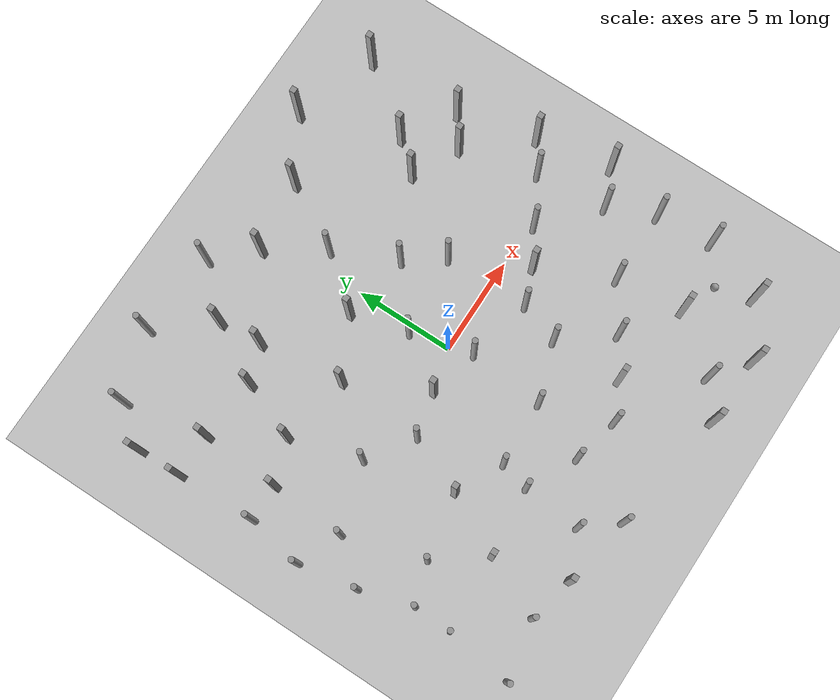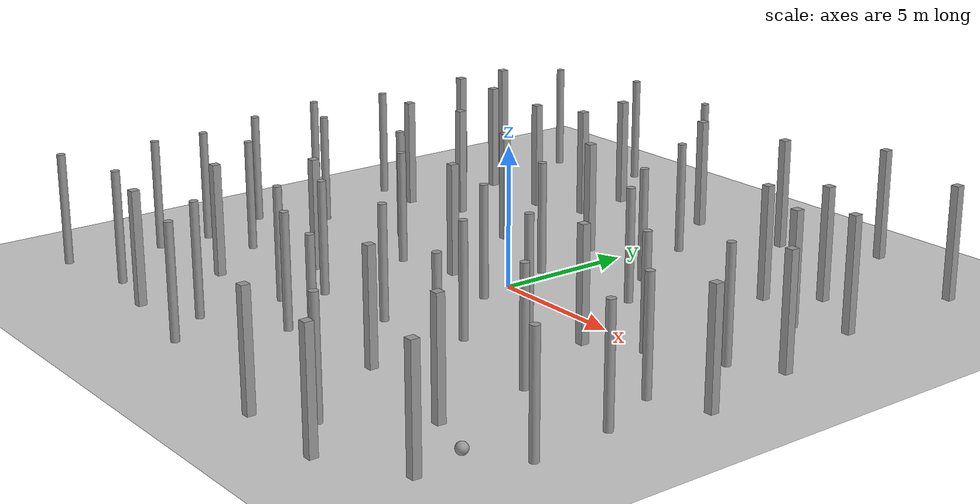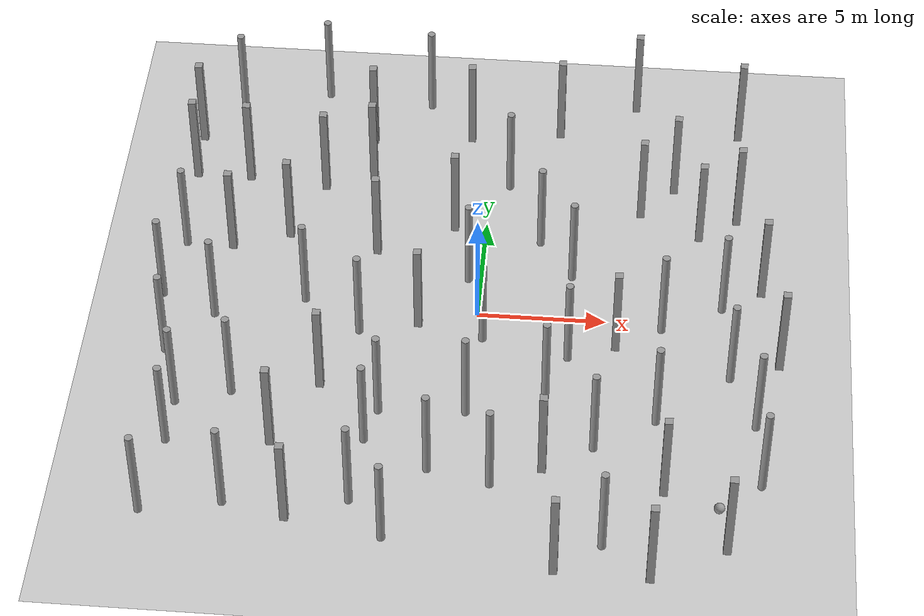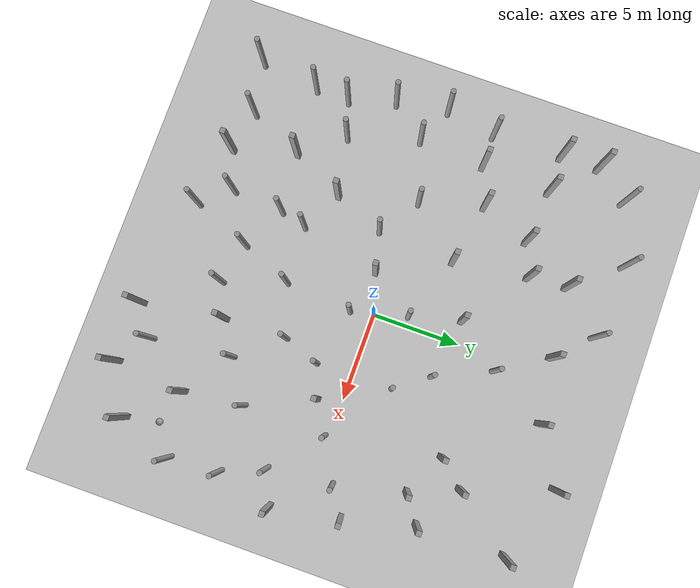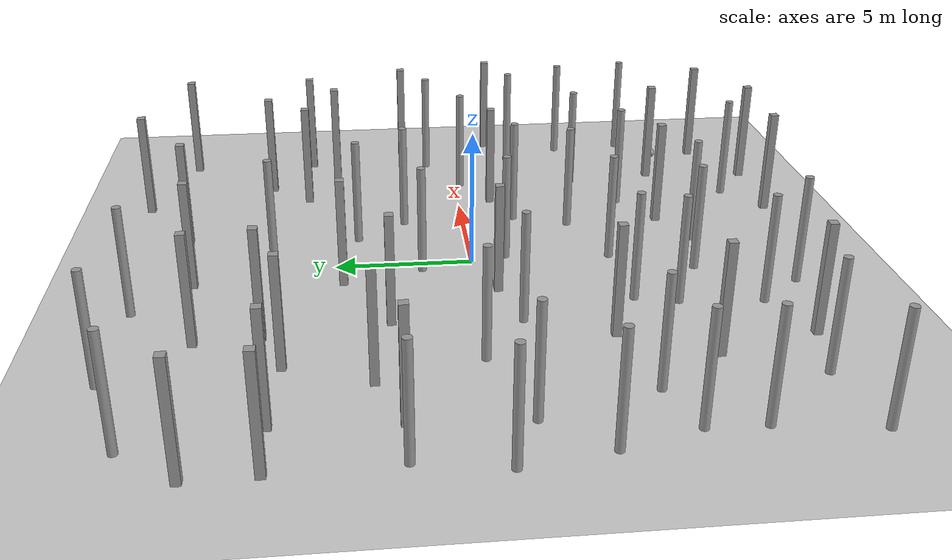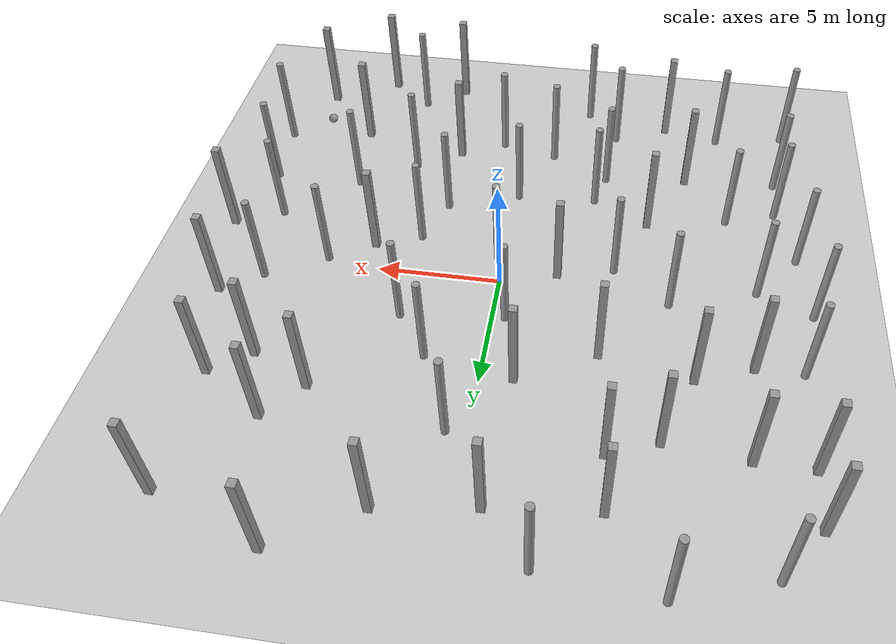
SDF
<sdf version="1.6">
 <world name="default">
  <light name="sun" type="directional">
   <pose>0 0 10 0 -0 0</pose>
   <diffuse>0.8 0.8 0.8 1</diffuse>
   <specular>0.2 0.2 0.2 1</specular>
   <attenuation>
    <range>1000</range>
    <constant>0.9</constant>
    <linear>0.01</linear>
    <quadratic>0.001</quadratic>
   </attenuation>
   <direction>-0.5 0.1 -0.9</direction>
  </light>
  <model name="ground_plane">
   <static>1</static>
   <link name="link">
    <collision name="collision">
     <geometry><plane><normal>0 0 1</normal><size>100 100</size></plane></geometry>
    </collision>
    <visual name="visual">
     <cast_shadows>0</cast_shadows>
     <geometry><plane><normal>0 0 1</normal><size>100 100</size></plane></geometry>
     <material>
      <script><uri>file://media/materials/scripts/gazebo.material</uri><name>Gazebo/Gray</name></script>
     </material>
    </visual>
   </link>
  </model>
  <gravity>0 0 -9.8</gravity>
  <magnetic_field>6e-06 2.3e-05 -4.2e-05</magnetic_field>
  <atmosphere type="adiabatic"/>
  <physics name="default_physics" default="0" type="ode">
   <max_step_size>0.002</max_step_size>
   <real_time_factor>1</real_time_factor>
   <real_time_update_rate>500</real_time_update_rate>
  </physics>
  <scene><ambient>0.4 0.4 0.4 1</ambient><background>0.7 0.7 0.7 1</background><shadows>1</shadows></scene>
  <spherical_coordinates>
   <surface_model>EARTH_WGS84</surface_model>
   <latitude_deg>0</latitude_deg>
   <longitude_deg>0</longitude_deg>
   <elevation>0</elevation>
   <heading_deg>0</heading_deg>
  </spherical_coordinates>
  <model name="unit_sphere">
   <link name="link">
    <inertial>
     <mass>1</mass>
     <inertia><ixx>0.1</ixx><ixy>0</ixy><ixz>0</ixz><iyy>0.1</iyy><iyz>0</iyz><izz>0.1</izz></inertia>
    </inertial>
    <gravity>0</gravity>
    <visual name="visual">
     <geometry><sphere><radius>0.203941</radius></sphere></geometry>
     <material>
      <script><name>Gazebo/Grey</name><uri>file://media/materials/scripts/gazebo.material</uri></script>
      <shader type="pixel"><normal_map>__default__</normal_map></shader>
     </material>
    </visual>
    <collision name="collision">
     <geometry><sphere><radius>0.203941</radius></sphere></geometry>
     <surface>
      <friction>
       <ode><mu>1</mu><mu2>1</mu2><fdir1>0 0 0</fdir1><slip1>0</slip1><slip2>0</slip2></ode>
       <torsional>
        <coefficient>1</coefficient>
        <patch_radius>0</patch_radius>
        <surface_radius>0</surface_radius>
        <use_patch_radius>1</use_patch_radius>
        <ode><slip>0</slip></ode>
       </torsional>
      </friction>
      <bounce><restitution_coefficient>0</restitution_coefficient><threshold>1e+06</threshold></bounce>
      <contact>
       <collide_without_contact>0</collide_without_contact>
       <collide_without_contact_bitmask>1</collide_without_contact_bitmask>
       <collide_bitmask>1</collide_bitmask>
       <ode>
        <soft_cfm>0</soft_cfm>
        <soft_erp>0.2</soft_erp>
        <kp>1e+13</kp>
        <kd>1</kd>
        <max_vel>0.01</max_vel>
        <min_depth>0</min_depth>
       </ode>
       <bullet>
        <split_impulse>1</split_impulse>
        <split_impulse_penetration_threshold>-0.01</split_impulse_penetration_threshold>
        <soft_cfm>0</soft_cfm>
        <soft_erp>0.2</soft_erp>
        <kp>1e+13</kp>
        <kd>1</kd>
       </bullet>
      </contact>
     </surface>
    </collision>
   </link>
   <static>0</static>
   <pose>9.54607 -9.14462 0.203941 0 -0 0</pose>
  </model>
  <audio><device>default</device></audio>
  <model name="unit_box">
   <link name="link">
    <inertial>
     <mass>1000</mass>
     <inertia><ixx>166.667</ixx><ixy>0</ixy><ixz>0</ixz><iyy>166.667</iyy><iyz>0</iyz><izz>166.667</izz></inertia>
    </inertial>
    <visual name="visual">
     <geometry><box><size>0.3 0.3 4</size></box></geometry>
     <material>
      <script><name>Gazebo/Grey</name><uri>file://media/materials/scripts/gazebo.material</uri></script>
      <shader type="vertex"><normal_map>__default__</normal_map></shader>
      <ambient>0.3 0.3 0.3 1</ambient>
      <diffuse>0.7 0.7 0.7 1</diffuse>
      <specular>0.01 0.01 0.01 1</specular>
      <emissive>0 0 0 1</emissive>
     </material>
    </visual>
    <collision name="collision">
     <geometry><box><size>0.3 0.3 4</size></box></geometry>
     <surface>
      <friction>
       <ode><mu>1</mu><mu2>1</mu2><fdir1>0 0 0</fdir1><slip1>0</slip1><slip2>0</slip2></ode>
       <torsional>
        <coefficient>1</coefficient>
        <patch_radius>0</patch_radius>
        <surface_radius>0</surface_radius>
        <use_patch_radius>1</use_patch_radius>
        <ode><slip>0</slip></ode>
       </torsional>
      </friction>
      <bounce><restitution_coefficient>0</restitution_coefficient><threshold>1e+06</threshold></bounce>
      <contact>
       <collide_without_contact>0</collide_without_contact>
       <collide_without_contact_bitmask>1</collide_without_contact_bitmask>
       <collide_bitmask>1</collide_bitmask>
       <ode>
        <soft_cfm>0</soft_cfm>
        <soft_erp>0.2</soft_erp>
        <kp>1e+13</kp>
        <kd>1</kd>
        <max_vel>0.01</max_vel>
        <min_depth>0</min_depth>
       </ode>
       <bullet>
        <split_impulse>1</split_impulse>
        <split_impulse_penetration_threshold>-0.01</split_impulse_penetration_threshold>
        <soft_cfm>0</soft_cfm>
        <soft_erp>0.2</soft_erp>
        <kp>1e+13</kp>
        <kd>1</kd>
       </bullet>
      </contact>
     </surface>
    </collision>
   </link>
   <static>0</static>
   <pose>-1.2673 4.71525 2 -9e-06 8e-06 -0.004085</pose>
  </model>
  <model name="unit_box_clone">
   <link name="link">
    <inertial>
     <mass>1000</mass>
     <inertia><ixx>166.667</ixx><ixy>0</ixy><ixz>0</ixz><iyy>166.667</iyy><iyz>0</iyz><izz>166.667</izz></inertia>
    </inertial>
    <visual name="visual">
     <geometry><box><size>0.3 0.3 4</size></box></geometry>
     <material>
      <script><name>Gazebo/Grey</name><uri>file://media/materials/scripts/gazebo.material</uri></script>
      <shader type="vertex"><normal_map>__default__</normal_map></shader>
      <ambient>0.3 0.3 0.3 1</ambient>
      <diffuse>0.7 0.7 0.7 1</diffuse>
      <specular>0.01 0.01 0.01 1</specular>
      <emissive>0 0 0 1</emissive>
     </material>
    </visual>
    <collision name="collision">
     <geometry><box><size>0.3 0.3 4</size></box></geometry>
     <surface>
      <friction>
       <ode><mu>1</mu><mu2>1</mu2><fdir1>0 0 0</fdir1><slip1>0</slip1><slip2>0</slip2></ode>
       <torsional>
        <coefficient>1</coefficient>
        <patch_radius>0</patch_radius>
        <surface_radius>0</surface_radius>
        <use_patch_radius>1</use_patch_radius>
        <ode><slip>0</slip></ode>
       </torsional>
      </friction>
      <bounce><restitution_coefficient>0</restitution_coefficient><threshold>1e+06</threshold></bounce>
      <contact>
       <collide_without_contact>0</collide_without_contact>
       <collide_without_contact_bitmask>1</collide_without_contact_bitmask>
       <collide_bitmask>1</collide_bitmask>
       <ode>
        <soft_cfm>0</soft_cfm>
        <soft_erp>0.2</soft_erp>
        <kp>1e+13</kp>
        <kd>1</kd>
        <max_vel>0.01</max_vel>
        <min_depth>0</min_depth>
       </ode>
       <bullet>
        <split_impulse>1</split_impulse>
        <split_impulse_penetration_threshold>-0.01</split_impulse_penetration_threshold>
        <soft_cfm>0</soft_cfm>
        <soft_erp>0.2</soft_erp>
        <kp>1e+13</kp>
        <kd>1</kd>
       </bullet>
      </contact>
     </surface>
    </collision>
   </link>
   <static>0</static>
   <pose>-2.25021 -0.681118 2.00001 4.2e-05 -5e-06 -0.00608</pose>
  </model>
  <model name="unit_box_clone_3">
   <link name="link">
    <inertial>
     <mass>1000</mass>
     <inertia><ixx>166.667</ixx><ixy>0</ixy><ixz>0</ixz><iyy>166.667</iyy><iyz>0</iyz><izz>166.667</izz></inertia>
    </inertial>
    <visual name="visual">
     <geometry><box><size>0.3 0.3 4</size></box></geometry>
     <material>
      <script><name>Gazebo/Grey</name><uri>file://media/materials/scripts/gazebo.material</uri></script>
      <shader type="vertex"><normal_map>__default__</normal_map></shader>
      <ambient>0.3 0.3 0.3 1</ambient>
      <diffuse>0.7 0.7 0.7 1</diffuse>
      <specular>0.01 0.01 0.01 1</specular>
      <emissive>0 0 0 1</emissive>
     </material>
    </visual>
    <collision name="collision">
     <geometry><box><size>0.3 0.3 4</size></box></geometry>
     <surface>
      <friction>
       <ode><mu>1</mu><mu2>1</mu2><fdir1>0 0 0</fdir1><slip1>0</slip1><slip2>0</slip2></ode>
       <torsional>
        <coefficient>1</coefficient>
        <patch_radius>0</patch_radius>
        <surface_radius>0</surface_radius>
        <use_patch_radius>1</use_patch_radius>
        <ode><slip>0</slip></ode>
       </torsional>
      </friction>
      <bounce><restitution_coefficient>0</restitution_coefficient><threshold>1e+06</threshold></bounce>
      <contact>
       <collide_without_contact>0</collide_without_contact>
       <collide_without_contact_bitmask>1</collide_without_contact_bitmask>
       <collide_bitmask>1</collide_bitmask>
       <ode>
        <soft_cfm>0</soft_cfm>
        <soft_erp>0.2</soft_erp>
        <kp>1e+13</kp>
        <kd>1</kd>
        <max_vel>0.01</max_vel>
        <min_depth>0</min_depth>
       </ode>
       <bullet>
        <split_impulse>1</split_impulse>
        <split_impulse_penetration_threshold>-0.01</split_impulse_penetration_threshold>
        <soft_cfm>0</soft_cfm>
        <soft_erp>0.2</soft_erp>
        <kp>1e+13</kp>
        <kd>1</kd>
       </bullet>
      </contact>
     </surface>
    </collision>
   </link>
   <static>0</static>
   <pose>-9.81583 6.97363 2 -7e-06 -7e-06 -0.004361</pose>
  </model>
  <model name="unit_box_clone_4">
   <link name="link">
    <inertial>
     <mass>1000</mass>
     <inertia><ixx>166.667</ixx><ixy>0</ixy><ixz>0</ixz><iyy>166.667</iyy><iyz>0</iyz><izz>166.667</izz></inertia>
    </inertial>
    <visual name="visual">
     <geometry><box><size>0.3 0.3 4</size></box></geometry>
     <material>
      <script><name>Gazebo/Grey</name><uri>file://media/materials/scripts/gazebo.material</uri></script>
      <shader type="vertex"><normal_map>__default__</normal_map></shader>
      <ambient>0.3 0.3 0.3 1</ambient>
      <diffuse>0.7 0.7 0.7 1</diffuse>
      <specular>0.01 0.01 0.01 1</specular>
      <emissive>0 0 0 1</emissive>
     </material>
    </visual>
    <collision name="collision">
     <geometry><box><size>0.3 0.3 4</size></box></geometry>
     <surface>
      <friction>
       <ode><mu>1</mu><mu2>1</mu2><fdir1>0 0 0</fdir1><slip1>0</slip1><slip2>0</slip2></ode>
       <torsional>
        <coefficient>1</coefficient>
        <patch_radius>0</patch_radius>
        <surface_radius>0</surface_radius>
        <use_patch_radius>1</use_patch_radius>
        <ode><slip>0</slip></ode>
       </torsional>
      </friction>
      <bounce><restitution_coefficient>0</restitution_coefficient><threshold>1e+06</threshold></bounce>
      <contact>
       <collide_without_contact>0</collide_without_contact>
       <collide_without_contact_bitmask>1</collide_without_contact_bitmask>
       <collide_bitmask>1</collide_bitmask>
       <ode>
        <soft_cfm>0</soft_cfm>
        <soft_erp>0.2</soft_erp>
        <kp>1e+13</kp>
        <kd>1</kd>
        <max_vel>0.01</max_vel>
        <min_depth>0</min_depth>
       </ode>
       <bullet>
        <split_impulse>1</split_impulse>
        <split_impulse_penetration_threshold>-0.01</split_impulse_penetration_threshold>
        <soft_cfm>0</soft_cfm>
        <soft_erp>0.2</soft_erp>
        <kp>1e+13</kp>
        <kd>1</kd>
       </bullet>
      </contact>
     </surface>
    </collision>
   </link>
   <static>0</static>
   <pose>-12.064 9.20918 2 2e-06 -4e-06 -0.001687</pose>
  </model>
  <model name="unit_box_clone_7">
   <link name="link">
    <inertial>
     <mass>1000</mass>
     <inertia><ixx>166.667</ixx><ixy>0</ixy><ixz>0</ixz><iyy>166.667</iyy><iyz>0</iyz><izz>166.667</izz></inertia>
    </inertial>
    <visual name="visual">
     <geometry><box><size>0.3 0.3 4</size></box></geometry>
     <material>
      <script><name>Gazebo/Grey</name><uri>file://media/materials/scripts/gazebo.material</uri></script>
      <shader type="vertex"><normal_map>__default__</normal_map></shader>
      <ambient>0.3 0.3 0.3 1</ambient>
      <diffuse>0.7 0.7 0.7 1</diffuse>
      <specular>0.01 0.01 0.01 1</specular>
      <emissive>0 0 0 1</emissive>
     </material>
    </visual>
    <collision name="collision">
     <geometry><box><size>0.3 0.3 4</size></box></geometry>
     <surface>
      <friction>
       <ode><mu>1</mu><mu2>1</mu2><fdir1>0 0 0</fdir1><slip1>0</slip1><slip2>0</slip2></ode>
       <torsional>
        <coefficient>1</coefficient>
        <patch_radius>0</patch_radius>
        <surface_radius>0</surface_radius>
        <use_patch_radius>1</use_patch_radius>
        <ode><slip>0</slip></ode>
       </torsional>
      </friction>
      <bounce><restitution_coefficient>0</restitution_coefficient><threshold>1e+06</threshold></bounce>
      <contact>
       <collide_without_contact>0</collide_without_contact>
       <collide_without_contact_bitmask>1</collide_without_contact_bitmask>
       <collide_bitmask>1</collide_bitmask>
       <ode>
        <soft_cfm>0</soft_cfm>
        <soft_erp>0.2</soft_erp>
        <kp>1e+13</kp>
        <kd>1</kd>
        <max_vel>0.01</max_vel>
        <min_depth>0</min_depth>
       </ode>
       <bullet>
        <split_impulse>1</split_impulse>
        <split_impulse_penetration_threshold>-0.01</split_impulse_penetration_threshold>
        <soft_cfm>0</soft_cfm>
        <soft_erp>0.2</soft_erp>
        <kp>1e+13</kp>
        <kd>1</kd>
       </bullet>
      </contact>
     </surface>
    </collision>
   </link>
   <static>0</static>
   <pose>9.86051 -10.9629 2 -2e-06 -2.1e-05 -0.007326</pose>
  </model>
  <model name="unit_box_clone_8">
   <link name="link">
    <inertial>
     <mass>1000</mass>
     <inertia><ixx>166.667</ixx><ixy>0</ixy><ixz>0</ixz><iyy>166.667</iyy><iyz>0</iyz><izz>166.667</izz></inertia>
    </inertial>
    <visual name="visual">
     <geometry><box><size>0.3 0.3 4</size></box></geometry>
     <material>
      <script><name>Gazebo/Grey</name><uri>file://media/materials/scripts/gazebo.material</uri></script>
      <shader type="vertex"><normal_map>__default__</normal_map></shader>
      <ambient>0.3 0.3 0.3 1</ambient>
      <diffuse>0.7 0.7 0.7 1</diffuse>
      <specular>0.01 0.01 0.01 1</specular>
      <emissive>0 0 0 1</emissive>
     </material>
    </visual>
    <collision name="collision">
     <geometry><box><size>0.3 0.3 4</size></box></geometry>
     <surface>
      <friction>
       <ode><mu>1</mu><mu2>1</mu2><fdir1>0 0 0</fdir1><slip1>0</slip1><slip2>0</slip2></ode>
       <torsional>
        <coefficient>1</coefficient>
        <patch_radius>0</patch_radius>
        <surface_radius>0</surface_radius>
        <use_patch_radius>1</use_patch_radius>
        <ode><slip>0</slip></ode>
       </torsional>
      </friction>
      <bounce><restitution_coefficient>0</restitution_coefficient><threshold>1e+06</threshold></bounce>
      <contact>
       <collide_without_contact>0</collide_without_contact>
       <collide_without_contact_bitmask>1</collide_without_contact_bitmask>
       <collide_bitmask>1</collide_bitmask>
       <ode>
        <soft_cfm>0</soft_cfm>
        <soft_erp>0.2</soft_erp>
        <kp>1e+13</kp>
        <kd>1</kd>
        <max_vel>0.01</max_vel>
        <min_depth>0</min_depth>
       </ode>
       <bullet>
        <split_impulse>1</split_impulse>
        <split_impulse_penetration_threshold>-0.01</split_impulse_penetration_threshold>
        <soft_cfm>0</soft_cfm>
        <soft_erp>0.2</soft_erp>
        <kp>1e+13</kp>
        <kd>1</kd>
       </bullet>
      </contact>
     </surface>
    </collision>
   </link>
   <static>0</static>
   <pose>-6.6889 6.67573 2 -8e-06 -4e-06 0.003592</pose>
  </model>
  <model name="unit_box_clone_13">
   <link name="link">
    <inertial>
     <mass>1000</mass>
     <inertia><ixx>166.667</ixx><ixy>0</ixy><ixz>0</ixz><iyy>166.667</iyy><iyz>0</iyz><izz>166.667</izz></inertia>
    </inertial>
    <visual name="visual">
     <geometry><box><size>0.3 0.3 4</size></box></geometry>
     <material>
      <script><name>Gazebo/Grey</name><uri>file://media/materials/scripts/gazebo.material</uri></script>
      <shader type="vertex"><normal_map>__default__</normal_map></shader>
      <ambient>0.3 0.3 0.3 1</ambient>
      <diffuse>0.7 0.7 0.7 1</diffuse>
      <specular>0.01 0.01 0.01 1</specular>
      <emissive>0 0 0 1</emissive>
     </material>
    </visual>
    <collision name="collision">
     <geometry><box><size>0.3 0.3 4</size></box></geometry>
     <surface>
      <friction>
       <ode><mu>1</mu><mu2>1</mu2><fdir1>0 0 0</fdir1><slip1>0</slip1><slip2>0</slip2></ode>
       <torsional>
        <coefficient>1</coefficient>
        <patch_radius>0</patch_radius>
        <surface_radius>0</surface_radius>
        <use_patch_radius>1</use_patch_radius>
        <ode><slip>0</slip></ode>
       </torsional>
      </friction>
      <bounce><restitution_coefficient>0</restitution_coefficient><threshold>1e+06</threshold></bounce>
      <contact>
       <collide_without_contact>0</collide_without_contact>
       <collide_without_contact_bitmask>1</collide_without_contact_bitmask>
       <collide_bitmask>1</collide_bitmask>
       <ode>
        <soft_cfm>0</soft_cfm>
        <soft_erp>0.2</soft_erp>
        <kp>1e+13</kp>
        <kd>1</kd>
        <max_vel>0.01</max_vel>
        <min_depth>0</min_depth>
       </ode>
       <bullet>
        <split_impulse>1</split_impulse>
        <split_impulse_penetration_threshold>-0.01</split_impulse_penetration_threshold>
        <soft_cfm>0</soft_cfm>
        <soft_erp>0.2</soft_erp>
        <kp>1e+13</kp>
        <kd>1</kd>
       </bullet>
      </contact>
     </surface>
    </collision>
   </link>
   <static>0</static>
   <pose>-10.0001 3.00008 2 -1e-06 -0 -0.00029</pose>
  </model>
  <model name="unit_box_clone_14">
   <link name="link">
    <inertial>
     <mass>1000</mass>
     <inertia><ixx>166.667</ixx><ixy>0</ixy><ixz>0</ixz><iyy>166.667</iyy><iyz>0</iyz><izz>166.667</izz></inertia>
    </inertial>
    <visual name="visual">
     <geometry><box><size>0.3 0.3 4</size></box></geometry>
     <material>
      <script><name>Gazebo/Grey</name><uri>file://media/materials/scripts/gazebo.material</uri></script>
      <shader type="vertex"><normal_map>__default__</normal_map></shader>
      <ambient>0.3 0.3 0.3 1</ambient>
      <diffuse>0.7 0.7 0.7 1</diffuse>
      <specular>0.01 0.01 0.01 1</specular>
      <emissive>0 0 0 1</emissive>
     </material>
    </visual>
    <collision name="collision">
     <geometry><box><size>0.3 0.3 4</size></box></geometry>
     <surface>
      <friction>
       <ode><mu>1</mu><mu2>1</mu2><fdir1>0 0 0</fdir1><slip1>0</slip1><slip2>0</slip2></ode>
       <torsional>
        <coefficient>1</coefficient>
        <patch_radius>0</patch_radius>
        <surface_radius>0</surface_radius>
        <use_patch_radius>1</use_patch_radius>
        <ode><slip>0</slip></ode>
       </torsional>
      </friction>
      <bounce><restitution_coefficient>0</restitution_coefficient><threshold>1e+06</threshold></bounce>
      <contact>
       <collide_without_contact>0</collide_without_contact>
       <collide_without_contact_bitmask>1</collide_without_contact_bitmask>
       <collide_bitmask>1</collide_bitmask>
       <ode>
        <soft_cfm>0</soft_cfm>
        <soft_erp>0.2</soft_erp>
        <kp>1e+13</kp>
        <kd>1</kd>
        <max_vel>0.01</max_vel>
        <min_depth>0</min_depth>
       </ode>
       <bullet>
        <split_impulse>1</split_impulse>
        <split_impulse_penetration_threshold>-0.01</split_impulse_penetration_threshold>
        <soft_cfm>0</soft_cfm>
        <soft_erp>0.2</soft_erp>
        <kp>1e+13</kp>
        <kd>1</kd>
       </bullet>
      </contact>
     </surface>
    </collision>
   </link>
   <static>0</static>
   <pose>-11.9999 7.00011 2 0 -1e-06 0.00014</pose>
  </model>
  <model name="unit_box_clone_22">
   <link name="link">
    <inertial>
     <mass>1000</mass>
     <inertia><ixx>166.667</ixx><ixy>0</ixy><ixz>0</ixz><iyy>166.667</iyy><iyz>0</iyz><izz>166.667</izz></inertia>
    </inertial>
    <visual name="visual">
     <geometry><box><size>0.3 0.3 4</size></box></geometry>
     <material>
      <script><name>Gazebo/Grey</name><uri>file://media/materials/scripts/gazebo.material</uri></script>
      <shader type="vertex"><normal_map>__default__</normal_map></shader>
      <ambient>0.3 0.3 0.3 1</ambient>
      <diffuse>0.7 0.7 0.7 1</diffuse>
      <specular>0.01 0.01 0.01 1</specular>
      <emissive>0 0 0 1</emissive>
     </material>
    </visual>
    <collision name="collision">
     <geometry><box><size>0.3 0.3 4</size></box></geometry>
     <surface>
      <friction>
       <ode><mu>1</mu><mu2>1</mu2><fdir1>0 0 0</fdir1><slip1>0</slip1><slip2>0</slip2></ode>
       <torsional>
        <coefficient>1</coefficient>
        <patch_radius>0</patch_radius>
        <surface_radius>0</surface_radius>
        <use_patch_radius>1</use_patch_radius>
        <ode><slip>0</slip></ode>
       </torsional>
      </friction>
      <bounce><restitution_coefficient>0</restitution_coefficient><threshold>1e+06</threshold></bounce>
      <contact>
       <collide_without_contact>0</collide_without_contact>
       <collide_without_contact_bitmask>1</collide_without_contact_bitmask>
       <collide_bitmask>1</collide_bitmask>
       <ode>
        <soft_cfm>0</soft_cfm>
        <soft_erp>0.2</soft_erp>
        <kp>1e+13</kp>
        <kd>1</kd>
        <max_vel>0.01</max_vel>
        <min_depth>0</min_depth>
       </ode>
       <bullet>
        <split_impulse>1</split_impulse>
        <split_impulse_penetration_threshold>-0.01</split_impulse_penetration_threshold>
        <soft_cfm>0</soft_cfm>
        <soft_erp>0.2</soft_erp>
        <kp>1e+13</kp>
        <kd>1</kd>
       </bullet>
      </contact>
     </surface>
    </collision>
   </link>
   <static>0</static>
   <pose>-0.99992 9.99994 2 3e-06 -2.5e-05 -0.007767</pose>
  </model>
  <model name="unit_box_clone_23">
   <link name="link">
    <inertial>
     <mass>1000</mass>
     <inertia><ixx>166.667</ixx><ixy>0</ixy><ixz>0</ixz><iyy>166.667</iyy><iyz>0</iyz><izz>166.667</izz></inertia>
    </inertial>
    <visual name="visual">
     <geometry><box><size>0.3 0.3 4</size></box></geometry>
     <material>
      <script><name>Gazebo/Grey</name><uri>file://media/materials/scripts/gazebo.material</uri></script>
      <shader type="vertex"><normal_map>__default__</normal_map></shader>
      <ambient>0.3 0.3 0.3 1</ambient>
      <diffuse>0.7 0.7 0.7 1</diffuse>
      <specular>0.01 0.01 0.01 1</specular>
      <emissive>0 0 0 1</emissive>
     </material>
    </visual>
    <collision name="collision">
     <geometry><box><size>0.3 0.3 4</size></box></geometry>
     <surface>
      <friction>
       <ode><mu>1</mu><mu2>1</mu2><fdir1>0 0 0</fdir1><slip1>0</slip1><slip2>0</slip2></ode>
       <torsional>
        <coefficient>1</coefficient>
        <patch_radius>0</patch_radius>
        <surface_radius>0</surface_radius>
        <use_patch_radius>1</use_patch_radius>
        <ode><slip>0</slip></ode>
       </torsional>
      </friction>
      <bounce><restitution_coefficient>0</restitution_coefficient><threshold>1e+06</threshold></bounce>
      <contact>
       <collide_without_contact>0</collide_without_contact>
       <collide_without_contact_bitmask>1</collide_without_contact_bitmask>
       <collide_bitmask>1</collide_bitmask>
       <ode>
        <soft_cfm>0</soft_cfm>
        <soft_erp>0.2</soft_erp>
        <kp>1e+13</kp>
        <kd>1</kd>
        <max_vel>0.01</max_vel>
        <min_depth>0</min_depth>
       </ode>
       <bullet>
        <split_impulse>1</split_impulse>
        <split_impulse_penetration_threshold>-0.01</split_impulse_penetration_threshold>
        <soft_cfm>0</soft_cfm>
        <soft_erp>0.2</soft_erp>
        <kp>1e+13</kp>
        <kd>1</kd>
       </bullet>
      </contact>
     </surface>
    </collision>
   </link>
   <static>0</static>
   <pose>-5.00228 9.59191 2 -7e-06 -6e-06 -0.000148</pose>
  </model>
  <model name="unit_box_clone_24">
   <link name="link">
    <inertial>
     <mass>1000</mass>
     <inertia><ixx>166.667</ixx><ixy>0</ixy><ixz>0</ixz><iyy>166.667</iyy><iyz>0</iyz><izz>166.667</izz></inertia>
    </inertial>
    <visual name="visual">
     <geometry><box><size>0.3 0.3 4</size></box></geometry>
     <material>
      <script><name>Gazebo/Grey</name><uri>file://media/materials/scripts/gazebo.material</uri></script>
      <shader type="vertex"><normal_map>__default__</normal_map></shader>
      <ambient>0.3 0.3 0.3 1</ambient>
      <diffuse>0.7 0.7 0.7 1</diffuse>
      <specular>0.01 0.01 0.01 1</specular>
      <emissive>0 0 0 1</emissive>
     </material>
    </visual>
    <collision name="collision">
     <geometry><box><size>0.3 0.3 4</size></box></geometry>
     <surface>
      <friction>
       <ode><mu>1</mu><mu2>1</mu2><fdir1>0 0 0</fdir1><slip1>0</slip1><slip2>0</slip2></ode>
       <torsional>
        <coefficient>1</coefficient>
        <patch_radius>0</patch_radius>
        <surface_radius>0</surface_radius>
        <use_patch_radius>1</use_patch_radius>
        <ode><slip>0</slip></ode>
       </torsional>
      </friction>
      <bounce><restitution_coefficient>0</restitution_coefficient><threshold>1e+06</threshold></bounce>
      <contact>
       <collide_without_contact>0</collide_without_contact>
       <collide_without_contact_bitmask>1</collide_without_contact_bitmask>
       <collide_bitmask>1</collide_bitmask>
       <ode>
        <soft_cfm>0</soft_cfm>
        <soft_erp>0.2</soft_erp>
        <kp>1e+13</kp>
        <kd>1</kd>
        <max_vel>0.01</max_vel>
        <min_depth>0</min_depth>
       </ode>
       <bullet>
        <split_impulse>1</split_impulse>
        <split_impulse_penetration_threshold>-0.01</split_impulse_penetration_threshold>
        <soft_cfm>0</soft_cfm>
        <soft_erp>0.2</soft_erp>
        <kp>1e+13</kp>
        <kd>1</kd>
       </bullet>
      </contact>
     </surface>
    </collision>
   </link>
   <static>0</static>
   <pose>-4.80942 7.40677 2.00001 -6.2e-05 -1e-06 0.003403</pose>
  </model>
  <model name="unit_box_clone_28">
   <link name="link">
    <inertial>
     <mass>1000</mass>
     <inertia><ixx>166.667</ixx><ixy>0</ixy><ixz>0</ixz><iyy>166.667</iyy><iyz>0</iyz><izz>166.667</izz></inertia>
    </inertial>
    <visual name="visual">
     <geometry><box><size>0.3 0.3 4</size></box></geometry>
     <material>
      <script><name>Gazebo/Grey</name><uri>file://media/materials/scripts/gazebo.material</uri></script>
      <shader type="vertex"><normal_map>__default__</normal_map></shader>
      <ambient>0.3 0.3 0.3 1</ambient>
      <diffuse>0.7 0.7 0.7 1</diffuse>
      <specular>0.01 0.01 0.01 1</specular>
      <emissive>0 0 0 1</emissive>
     </material>
    </visual>
    <collision name="collision">
     <geometry><box><size>0.3 0.3 4</size></box></geometry>
     <surface>
      <friction>
       <ode><mu>1</mu><mu2>1</mu2><fdir1>0 0 0</fdir1><slip1>0</slip1><slip2>0</slip2></ode>
       <torsional>
        <coefficient>1</coefficient>
        <patch_radius>0</patch_radius>
        <surface_radius>0</surface_radius>
        <use_patch_radius>1</use_patch_radius>
        <ode><slip>0</slip></ode>
       </torsional>
      </friction>
      <bounce><restitution_coefficient>0</restitution_coefficient><threshold>1e+06</threshold></bounce>
      <contact>
       <collide_without_contact>0</collide_without_contact>
       <collide_without_contact_bitmask>1</collide_without_contact_bitmask>
       <collide_bitmask>1</collide_bitmask>
       <ode>
        <soft_cfm>0</soft_cfm>
        <soft_erp>0.2</soft_erp>
        <kp>1e+13</kp>
        <kd>1</kd>
        <max_vel>0.01</max_vel>
        <min_depth>0</min_depth>
       </ode>
       <bullet>
        <split_impulse>1</split_impulse>
        <split_impulse_penetration_threshold>-0.01</split_impulse_penetration_threshold>
        <soft_cfm>0</soft_cfm>
        <soft_erp>0.2</soft_erp>
        <kp>1e+13</kp>
        <kd>1</kd>
       </bullet>
      </contact>
     </surface>
    </collision>
   </link>
   <static>0</static>
   <pose>-7.80117 3.8248 2 -4e-06 2e-06 -0.004554</pose>
  </model>
  <model name="unit_cylinder">
   <link name="link">
    <inertial>
     <mass>1000</mass>
     <inertia><ixx>145.833</ixx><ixy>0</ixy><ixz>0</ixz><iyy>145.833</iyy><iyz>0</iyz><izz>125</izz></inertia>
    </inertial>
    <visual name="visual">
     <geometry><cylinder><radius>0.15</radius><length>4</length></cylinder></geometry>
     <material>
      <script><name>Gazebo/Grey</name><uri>file://media/materials/scripts/gazebo.material</uri></script>
      <shader type="vertex"><normal_map>__default__</normal_map></shader>
      <ambient>0.3 0.3 0.3 1</ambient>
      <diffuse>0.7 0.7 0.7 1</diffuse>
      <specular>0.01 0.01 0.01 1</specular>
      <emissive>0 0 0 1</emissive>
     </material>
    </visual>
    <collision name="collision">
     <geometry><cylinder><radius>0.15</radius><length>4</length></cylinder></geometry>
     <surface>
      <friction>
       <ode><mu>1</mu><mu2>1</mu2><fdir1>0 0 0</fdir1><slip1>0</slip1><slip2>0</slip2></ode>
       <torsional>
        <coefficient>1</coefficient>
        <patch_radius>0</patch_radius>
        <surface_radius>0</surface_radius>
        <use_patch_radius>1</use_patch_radius>
        <ode><slip>0</slip></ode>
       </torsional>
      </friction>
      <bounce><restitution_coefficient>0</restitution_coefficient><threshold>1e+06</threshold></bounce>
      <contact>
       <collide_without_contact>0</collide_without_contact>
       <collide_without_contact_bitmask>1</collide_without_contact_bitmask>
       <collide_bitmask>1</collide_bitmask>
       <ode>
        <soft_cfm>0</soft_cfm>
        <soft_erp>0.2</soft_erp>
        <kp>1e+13</kp>
        <kd>1</kd>
        <max_vel>0.01</max_vel>
        <min_depth>0</min_depth>
       </ode>
       <bullet>
        <split_impulse>1</split_impulse>
        <split_impulse_penetration_threshold>-0.01</split_impulse_penetration_threshold>
        <soft_cfm>0</soft_cfm>
        <soft_erp>0.2</soft_erp>
        <kp>1e+13</kp>
        <kd>1</kd>
       </bullet>
      </contact>
     </surface>
    </collision>
   </link>
   <static>0</static>
   <pose>3.55788 2.30314 1.99998 -2e-06 -0 -0.201387</pose>
  </model>
  <model name="unit_cylinder_clone_3">
   <link name="link">
    <inertial>
     <mass>1000</mass>
     <inertia><ixx>145.833</ixx><ixy>0</ixy><ixz>0</ixz><iyy>145.833</iyy><iyz>0</iyz><izz>125</izz></inertia>
    </inertial>
    <visual name="visual">
     <geometry><cylinder><radius>0.15</radius><length>4</length></cylinder></geometry>
     <material>
      <script><name>Gazebo/Grey</name><uri>file://media/materials/scripts/gazebo.material</uri></script>
      <shader type="vertex"><normal_map>__default__</normal_map></shader>
      <ambient>0.3 0.3 0.3 1</ambient>
      <diffuse>0.7 0.7 0.7 1</diffuse>
      <specular>0.01 0.01 0.01 1</specular>
      <emissive>0 0 0 1</emissive>
     </material>
    </visual>
    <collision name="collision">
     <geometry><cylinder><radius>0.15</radius><length>4</length></cylinder></geometry>
     <surface>
      <friction>
       <ode><mu>1</mu><mu2>1</mu2><fdir1>0 0 0</fdir1><slip1>0</slip1><slip2>0</slip2></ode>
       <torsional>
        <coefficient>1</coefficient>
        <patch_radius>0</patch_radius>
        <surface_radius>0</surface_radius>
        <use_patch_radius>1</use_patch_radius>
        <ode><slip>0</slip></ode>
       </torsional>
      </friction>
      <bounce><restitution_coefficient>0</restitution_coefficient><threshold>1e+06</threshold></bounce>
      <contact>
       <collide_without_contact>0</collide_without_contact>
       <collide_without_contact_bitmask>1</collide_without_contact_bitmask>
       <collide_bitmask>1</collide_bitmask>
       <ode>
        <soft_cfm>0</soft_cfm>
        <soft_erp>0.2</soft_erp>
        <kp>1e+13</kp>
        <kd>1</kd>
        <max_vel>0.01</max_vel>
        <min_depth>0</min_depth>
       </ode>
       <bullet>
        <split_impulse>1</split_impulse>
        <split_impulse_penetration_threshold>-0.01</split_impulse_penetration_threshold>
        <soft_cfm>0</soft_cfm>
        <soft_erp>0.2</soft_erp>
        <kp>1e+13</kp>
        <kd>1</kd>
       </bullet>
      </contact>
     </surface>
    </collision>
   </link>
   <static>0</static>
   <pose>0.764098 7.25686 1.99998 -2e-06 -1e-06 -0.193878</pose>
  </model>
  <model name="unit_cylinder_clone_0_clone">
   <link name="link">
    <inertial>
     <mass>1000</mass>
     <inertia><ixx>145.833</ixx><ixy>0</ixy><ixz>0</ixz><iyy>145.833</iyy><iyz>0</iyz><izz>125</izz></inertia>
    </inertial>
    <visual name="visual">
     <geometry><cylinder><radius>0.15</radius><length>4</length></cylinder></geometry>
     <material>
      <script><name>Gazebo/Grey</name><uri>file://media/materials/scripts/gazebo.material</uri></script>
      <shader type="vertex"><normal_map>__default__</normal_map></shader>
      <ambient>0.3 0.3 0.3 1</ambient>
      <diffuse>0.7 0.7 0.7 1</diffuse>
      <specular>0.01 0.01 0.01 1</specular>
      <emissive>0 0 0 1</emissive>
     </material>
    </visual>
    <collision name="collision">
     <geometry><cylinder><radius>0.15</radius><length>4</length></cylinder></geometry>
     <surface>
      <friction>
       <ode><mu>1</mu><mu2>1</mu2><fdir1>0 0 0</fdir1><slip1>0</slip1><slip2>0</slip2></ode>
       <torsional>
        <coefficient>1</coefficient>
        <patch_radius>0</patch_radius>
        <surface_radius>0</surface_radius>
        <use_patch_radius>1</use_patch_radius>
        <ode><slip>0</slip></ode>
       </torsional>
      </friction>
      <bounce><restitution_coefficient>0</restitution_coefficient><threshold>1e+06</threshold></bounce>
      <contact>
       <collide_without_contact>0</collide_without_contact>
       <collide_without_contact_bitmask>1</collide_without_contact_bitmask>
       <collide_bitmask>1</collide_bitmask>
       <ode>
        <soft_cfm>0</soft_cfm>
        <soft_erp>0.2</soft_erp>
        <kp>1e+13</kp>
        <kd>1</kd>
        <max_vel>0.01</max_vel>
        <min_depth>0</min_depth>
       </ode>
       <bullet>
        <split_impulse>1</split_impulse>
        <split_impulse_penetration_threshold>-0.01</split_impulse_penetration_threshold>
        <soft_cfm>0</soft_cfm>
        <soft_erp>0.2</soft_erp>
        <kp>1e+13</kp>
        <kd>1</kd>
       </bullet>
      </contact>
     </surface>
    </collision>
   </link>
   <static>0</static>
   <pose>10.8485 -4.98906 1.99998 -1e-06 1e-06 -0.171576</pose>
  </model>
  <model name="unit_cylinder_clone_1_clone">
   <link name="link">
    <inertial>
     <mass>1000</mass>
     <inertia><ixx>145.833</ixx><ixy>0</ixy><ixz>0</ixz><iyy>145.833</iyy><iyz>0</iyz><izz>125</izz></inertia>
    </inertial>
    <visual name="visual">
     <geometry><cylinder><radius>0.15</radius><length>4</length></cylinder></geometry>
     <material>
      <script><name>Gazebo/Grey</name><uri>file://media/materials/scripts/gazebo.material</uri></script>
      <shader type="vertex"><normal_map>__default__</normal_map></shader>
      <ambient>0.3 0.3 0.3 1</ambient>
      <diffuse>0.7 0.7 0.7 1</diffuse>
      <specular>0.01 0.01 0.01 1</specular>
      <emissive>0 0 0 1</emissive>
     </material>
    </visual>
    <collision name="collision">
     <geometry><cylinder><radius>0.15</radius><length>4</length></cylinder></geometry>
     <surface>
      <friction>
       <ode><mu>1</mu><mu2>1</mu2><fdir1>0 0 0</fdir1><slip1>0</slip1><slip2>0</slip2></ode>
       <torsional>
        <coefficient>1</coefficient>
        <patch_radius>0</patch_radius>
        <surface_radius>0</surface_radius>
        <use_patch_radius>1</use_patch_radius>
        <ode><slip>0</slip></ode>
       </torsional>
      </friction>
      <bounce><restitution_coefficient>0</restitution_coefficient><threshold>1e+06</threshold></bounce>
      <contact>
       <collide_without_contact>0</collide_without_contact>
       <collide_without_contact_bitmask>1</collide_without_contact_bitmask>
       <collide_bitmask>1</collide_bitmask>
       <ode>
        <soft_cfm>0</soft_cfm>
        <soft_erp>0.2</soft_erp>
        <kp>1e+13</kp>
        <kd>1</kd>
        <max_vel>0.01</max_vel>
        <min_depth>0</min_depth>
       </ode>
       <bullet>
        <split_impulse>1</split_impulse>
        <split_impulse_penetration_threshold>-0.01</split_impulse_penetration_threshold>
        <soft_cfm>0</soft_cfm>
        <soft_erp>0.2</soft_erp>
        <kp>1e+13</kp>
        <kd>1</kd>
       </bullet>
      </contact>
     </surface>
    </collision>
   </link>
   <static>0</static>
   <pose>-1.25665 -8.01574 1.99995 -0.000271 -2.6e-05 -0.889031</pose>
  </model>
  <model name="unit_cylinder_clone_1_clone_1">
   <link name="link">
    <inertial>
     <mass>1000</mass>
     <inertia><ixx>145.833</ixx><ixy>0</ixy><ixz>0</ixz><iyy>145.833</iyy><iyz>0</iyz><izz>125</izz></inertia>
    </inertial>
    <visual name="visual">
     <geometry><cylinder><radius>0.15</radius><length>4</length></cylinder></geometry>
     <material>
      <script><name>Gazebo/Grey</name><uri>file://media/materials/scripts/gazebo.material</uri></script>
      <shader type="vertex"><normal_map>__default__</normal_map></shader>
      <ambient>0.3 0.3 0.3 1</ambient>
      <diffuse>0.7 0.7 0.7 1</diffuse>
      <specular>0.01 0.01 0.01 1</specular>
      <emissive>0 0 0 1</emissive>
     </material>
    </visual>
    <collision name="collision">
     <geometry><cylinder><radius>0.15</radius><length>4</length></cylinder></geometry>
     <surface>
      <friction>
       <ode><mu>1</mu><mu2>1</mu2><fdir1>0 0 0</fdir1><slip1>0</slip1><slip2>0</slip2></ode>
       <torsional>
        <coefficient>1</coefficient>
        <patch_radius>0</patch_radius>
        <surface_radius>0</surface_radius>
        <use_patch_radius>1</use_patch_radius>
        <ode><slip>0</slip></ode>
       </torsional>
      </friction>
      <bounce><restitution_coefficient>0</restitution_coefficient><threshold>1e+06</threshold></bounce>
      <contact>
       <collide_without_contact>0</collide_without_contact>
       <collide_without_contact_bitmask>1</collide_without_contact_bitmask>
       <collide_bitmask>1</collide_bitmask>
       <ode>
        <soft_cfm>0</soft_cfm>
        <soft_erp>0.2</soft_erp>
        <kp>1e+13</kp>
        <kd>1</kd>
        <max_vel>0.01</max_vel>
        <min_depth>0</min_depth>
       </ode>
       <bullet>
        <split_impulse>1</split_impulse>
        <split_impulse_penetration_threshold>-0.01</split_impulse_penetration_threshold>
        <soft_cfm>0</soft_cfm>
        <soft_erp>0.2</soft_erp>
        <kp>1e+13</kp>
        <kd>1</kd>
       </bullet>
      </contact>
     </surface>
    </collision>
   </link>
   <static>0</static>
   <pose>-11.8331 -2.81075 1.99995 -0.000271 -2.8e-05 -0.895331</pose>
  </model>
  <model name="unit_cylinder_clone_1_clone_2">
   <link name="link">
    <inertial>
     <mass>1000</mass>
     <inertia><ixx>145.833</ixx><ixy>0</ixy><ixz>0</ixz><iyy>145.833</iyy><iyz>0</iyz><izz>125</izz></inertia>
    </inertial>
    <visual name="visual">
     <geometry><cylinder><radius>0.15</radius><length>4</length></cylinder></geometry>
     <material>
      <script><name>Gazebo/Grey</name><uri>file://media/materials/scripts/gazebo.material</uri></script>
      <shader type="vertex"><normal_map>__default__</normal_map></shader>
      <ambient>0.3 0.3 0.3 1</ambient>
      <diffuse>0.7 0.7 0.7 1</diffuse>
      <specular>0.01 0.01 0.01 1</specular>
      <emissive>0 0 0 1</emissive>
     </material>
    </visual>
    <collision name="collision">
     <geometry><cylinder><radius>0.15</radius><length>4</length></cylinder></geometry>
     <surface>
      <friction>
       <ode><mu>1</mu><mu2>1</mu2><fdir1>0 0 0</fdir1><slip1>0</slip1><slip2>0</slip2></ode>
       <torsional>
        <coefficient>1</coefficient>
        <patch_radius>0</patch_radius>
        <surface_radius>0</surface_radius>
        <use_patch_radius>1</use_patch_radius>
        <ode><slip>0</slip></ode>
       </torsional>
      </friction>
      <bounce><restitution_coefficient>0</restitution_coefficient><threshold>1e+06</threshold></bounce>
      <contact>
       <collide_without_contact>0</collide_without_contact>
       <collide_without_contact_bitmask>1</collide_without_contact_bitmask>
       <collide_bitmask>1</collide_bitmask>
       <ode>
        <soft_cfm>0</soft_cfm>
        <soft_erp>0.2</soft_erp>
        <kp>1e+13</kp>
        <kd>1</kd>
        <max_vel>0.01</max_vel>
        <min_depth>0</min_depth>
       </ode>
       <bullet>
        <split_impulse>1</split_impulse>
        <split_impulse_penetration_threshold>-0.01</split_impulse_penetration_threshold>
        <soft_cfm>0</soft_cfm>
        <soft_erp>0.2</soft_erp>
        <kp>1e+13</kp>
        <kd>1</kd>
       </bullet>
      </contact>
     </surface>
    </collision>
   </link>
   <static>0</static>
   <pose>-3.73047 -6.76346 1.99995 -0.000271 -2.6e-05 -0.89068</pose>
  </model>
  <model name="unit_cylinder_clone_1_clone_4">
   <link name="link">
    <inertial>
     <mass>1000</mass>
     <inertia><ixx>145.833</ixx><ixy>0</ixy><ixz>0</ixz><iyy>145.833</iyy><iyz>0</iyz><izz>125</izz></inertia>
    </inertial>
    <visual name="visual">
     <geometry><cylinder><radius>0.15</radius><length>4</length></cylinder></geometry>
     <material>
      <script><name>Gazebo/Grey</name><uri>file://media/materials/scripts/gazebo.material</uri></script>
      <shader type="vertex"><normal_map>__default__</normal_map></shader>
      <ambient>0.3 0.3 0.3 1</ambient>
      <diffuse>0.7 0.7 0.7 1</diffuse>
      <specular>0.01 0.01 0.01 1</specular>
      <emissive>0 0 0 1</emissive>
     </material>
    </visual>
    <collision name="collision">
     <geometry><cylinder><radius>0.15</radius><length>4</length></cylinder></geometry>
     <surface>
      <friction>
       <ode><mu>1</mu><mu2>1</mu2><fdir1>0 0 0</fdir1><slip1>0</slip1><slip2>0</slip2></ode>
       <torsional>
        <coefficient>1</coefficient>
        <patch_radius>0</patch_radius>
        <surface_radius>0</surface_radius>
        <use_patch_radius>1</use_patch_radius>
        <ode><slip>0</slip></ode>
       </torsional>
      </friction>
      <bounce><restitution_coefficient>0</restitution_coefficient><threshold>1e+06</threshold></bounce>
      <contact>
       <collide_without_contact>0</collide_without_contact>
       <collide_without_contact_bitmask>1</collide_without_contact_bitmask>
       <collide_bitmask>1</collide_bitmask>
       <ode>
        <soft_cfm>0</soft_cfm>
        <soft_erp>0.2</soft_erp>
        <kp>1e+13</kp>
        <kd>1</kd>
        <max_vel>0.01</max_vel>
        <min_depth>0</min_depth>
       </ode>
       <bullet>
        <split_impulse>1</split_impulse>
        <split_impulse_penetration_threshold>-0.01</split_impulse_penetration_threshold>
        <soft_cfm>0</soft_cfm>
        <soft_erp>0.2</soft_erp>
        <kp>1e+13</kp>
        <kd>1</kd>
       </bullet>
      </contact>
     </surface>
    </collision>
   </link>
   <static>0</static>
   <pose>-8.98869 -4.76176 1.99995 -0.000271 -2.8e-05 -0.897295</pose>
  </model>
  <model name="unit_cylinder_clone_1_clone_6">
   <link name="link">
    <inertial>
     <mass>1000</mass>
     <inertia><ixx>145.833</ixx><ixy>0</ixy><ixz>0</ixz><iyy>145.833</iyy><iyz>0</iyz><izz>125</izz></inertia>
    </inertial>
    <visual name="visual">
     <geometry><cylinder><radius>0.15</radius><length>4</length></cylinder></geometry>
     <material>
      <script><name>Gazebo/Grey</name><uri>file://media/materials/scripts/gazebo.material</uri></script>
      <shader type="vertex"><normal_map>__default__</normal_map></shader>
      <ambient>0.3 0.3 0.3 1</ambient>
      <diffuse>0.7 0.7 0.7 1</diffuse>
      <specular>0.01 0.01 0.01 1</specular>
      <emissive>0 0 0 1</emissive>
     </material>
    </visual>
    <collision name="collision">
     <geometry><cylinder><radius>0.15</radius><length>4</length></cylinder></geometry>
     <surface>
      <friction>
       <ode><mu>1</mu><mu2>1</mu2><fdir1>0 0 0</fdir1><slip1>0</slip1><slip2>0</slip2></ode>
       <torsional>
        <coefficient>1</coefficient>
        <patch_radius>0</patch_radius>
        <surface_radius>0</surface_radius>
        <use_patch_radius>1</use_patch_radius>
        <ode><slip>0</slip></ode>
       </torsional>
      </friction>
      <bounce><restitution_coefficient>0</restitution_coefficient><threshold>1e+06</threshold></bounce>
      <contact>
       <collide_without_contact>0</collide_without_contact>
       <collide_without_contact_bitmask>1</collide_without_contact_bitmask>
       <collide_bitmask>1</collide_bitmask>
       <ode>
        <soft_cfm>0</soft_cfm>
        <soft_erp>0.2</soft_erp>
        <kp>1e+13</kp>
        <kd>1</kd>
        <max_vel>0.01</max_vel>
        <min_depth>0</min_depth>
       </ode>
       <bullet>
        <split_impulse>1</split_impulse>
        <split_impulse_penetration_threshold>-0.01</split_impulse_penetration_threshold>
        <soft_cfm>0</soft_cfm>
        <soft_erp>0.2</soft_erp>
        <kp>1e+13</kp>
        <kd>1</kd>
       </bullet>
      </contact>
     </surface>
    </collision>
   </link>
   <static>0</static>
   <pose>-3.34469 -5.28289 1.99998 -1e-06 1e-06 -0.209365</pose>
  </model>
  <model name="unit_cylinder_clone_1_clone_8">
   <link name="link">
    <inertial>
     <mass>1000</mass>
     <inertia><ixx>145.833</ixx><ixy>0</ixy><ixz>0</ixz><iyy>145.833</iyy><iyz>0</iyz><izz>125</izz></inertia>
    </inertial>
    <visual name="visual">
     <geometry><cylinder><radius>0.15</radius><length>4</length></cylinder></geometry>
     <material>
      <script><name>Gazebo/Grey</name><uri>file://media/materials/scripts/gazebo.material</uri></script>
      <shader type="vertex"><normal_map>__default__</normal_map></shader>
      <ambient>0.3 0.3 0.3 1</ambient>
      <diffuse>0.7 0.7 0.7 1</diffuse>
      <specular>0.01 0.01 0.01 1</specular>
      <emissive>0 0 0 1</emissive>
     </material>
    </visual>
    <collision name="collision">
     <geometry><cylinder><radius>0.15</radius><length>4</length></cylinder></geometry>
     <surface>
      <friction>
       <ode><mu>1</mu><mu2>1</mu2><fdir1>0 0 0</fdir1><slip1>0</slip1><slip2>0</slip2></ode>
       <torsional>
        <coefficient>1</coefficient>
        <patch_radius>0</patch_radius>
        <surface_radius>0</surface_radius>
        <use_patch_radius>1</use_patch_radius>
        <ode><slip>0</slip></ode>
       </torsional>
      </friction>
      <bounce><restitution_coefficient>0</restitution_coefficient><threshold>1e+06</threshold></bounce>
      <contact>
       <collide_without_contact>0</collide_without_contact>
       <collide_without_contact_bitmask>1</collide_without_contact_bitmask>
       <collide_bitmask>1</collide_bitmask>
       <ode>
        <soft_cfm>0</soft_cfm>
        <soft_erp>0.2</soft_erp>
        <kp>1e+13</kp>
        <kd>1</kd>
        <max_vel>0.01</max_vel>
        <min_depth>0</min_depth>
       </ode>
       <bullet>
        <split_impulse>1</split_impulse>
        <split_impulse_penetration_threshold>-0.01</split_impulse_penetration_threshold>
        <soft_cfm>0</soft_cfm>
        <soft_erp>0.2</soft_erp>
        <kp>1e+13</kp>
        <kd>1</kd>
       </bullet>
      </contact>
     </surface>
    </collision>
   </link>
   <static>0</static>
   <pose>0.289465 -1.27897 1.99995 -0.000271 -2.6e-05 -0.890373</pose>
  </model>
  <model name="unit_cylinder_clone_1_clone_9">
   <link name="link">
    <inertial>
     <mass>1000</mass>
     <inertia><ixx>145.833</ixx><ixy>0</ixy><ixz>0</ixz><iyy>145.833</iyy><iyz>0</iyz><izz>125</izz></inertia>
    </inertial>
    <visual name="visual">
     <geometry><cylinder><radius>0.15</radius><length>4</length></cylinder></geometry>
     <material>
      <script><name>Gazebo/Grey</name><uri>file://media/materials/scripts/gazebo.material</uri></script>
      <shader type="vertex"><normal_map>__default__</normal_map></shader>
      <ambient>0.3 0.3 0.3 1</ambient>
      <diffuse>0.7 0.7 0.7 1</diffuse>
      <specular>0.01 0.01 0.01 1</specular>
      <emissive>0 0 0 1</emissive>
     </material>
    </visual>
    <collision name="collision">
     <geometry><cylinder><radius>0.15</radius><length>4</length></cylinder></geometry>
     <surface>
      <friction>
       <ode><mu>1</mu><mu2>1</mu2><fdir1>0 0 0</fdir1><slip1>0</slip1><slip2>0</slip2></ode>
       <torsional>
        <coefficient>1</coefficient>
        <patch_radius>0</patch_radius>
        <surface_radius>0</surface_radius>
        <use_patch_radius>1</use_patch_radius>
        <ode><slip>0</slip></ode>
       </torsional>
      </friction>
      <bounce><restitution_coefficient>0</restitution_coefficient><threshold>1e+06</threshold></bounce>
      <contact>
       <collide_without_contact>0</collide_without_contact>
       <collide_without_contact_bitmask>1</collide_without_contact_bitmask>
       <collide_bitmask>1</collide_bitmask>
       <ode>
        <soft_cfm>0</soft_cfm>
        <soft_erp>0.2</soft_erp>
        <kp>1e+13</kp>
        <kd>1</kd>
        <max_vel>0.01</max_vel>
        <min_depth>0</min_depth>
       </ode>
       <bullet>
        <split_impulse>1</split_impulse>
        <split_impulse_penetration_threshold>-0.01</split_impulse_penetration_threshold>
        <soft_cfm>0</soft_cfm>
        <soft_erp>0.2</soft_erp>
        <kp>1e+13</kp>
        <kd>1</kd>
       </bullet>
      </contact>
     </surface>
    </collision>
   </link>
   <static>0</static>
   <pose>11.0861 -7.86396 1.99995 -0.000271 -2.7e-05 -0.891231</pose>
  </model>
  <model name="unit_cylinder_clone_1_clone_10">
   <link name="link">
    <inertial>
     <mass>1000</mass>
     <inertia><ixx>145.833</ixx><ixy>0</ixy><ixz>0</ixz><iyy>145.833</iyy><iyz>0</iyz><izz>125</izz></inertia>
    </inertial>
    <visual name="visual">
     <geometry><cylinder><radius>0.15</radius><length>4</length></cylinder></geometry>
     <material>
      <script><name>Gazebo/Grey</name><uri>file://media/materials/scripts/gazebo.material</uri></script>
      <shader type="vertex"><normal_map>__default__</normal_map></shader>
      <ambient>0.3 0.3 0.3 1</ambient>
      <diffuse>0.7 0.7 0.7 1</diffuse>
      <specular>0.01 0.01 0.01 1</specular>
      <emissive>0 0 0 1</emissive>
     </material>
    </visual>
    <collision name="collision">
     <geometry><cylinder><radius>0.15</radius><length>4</length></cylinder></geometry>
     <surface>
      <friction>
       <ode><mu>1</mu><mu2>1</mu2><fdir1>0 0 0</fdir1><slip1>0</slip1><slip2>0</slip2></ode>
       <torsional>
        <coefficient>1</coefficient>
        <patch_radius>0</patch_radius>
        <surface_radius>0</surface_radius>
        <use_patch_radius>1</use_patch_radius>
        <ode><slip>0</slip></ode>
       </torsional>
      </friction>
      <bounce><restitution_coefficient>0</restitution_coefficient><threshold>1e+06</threshold></bounce>
      <contact>
       <collide_without_contact>0</collide_without_contact>
       <collide_without_contact_bitmask>1</collide_without_contact_bitmask>
       <collide_bitmask>1</collide_bitmask>
       <ode>
        <soft_cfm>0</soft_cfm>
        <soft_erp>0.2</soft_erp>
        <kp>1e+13</kp>
        <kd>1</kd>
        <max_vel>0.01</max_vel>
        <min_depth>0</min_depth>
       </ode>
       <bullet>
        <split_impulse>1</split_impulse>
        <split_impulse_penetration_threshold>-0.01</split_impulse_penetration_threshold>
        <soft_cfm>0</soft_cfm>
        <soft_erp>0.2</soft_erp>
        <kp>1e+13</kp>
        <kd>1</kd>
       </bullet>
      </contact>
     </surface>
    </collision>
   </link>
   <static>0</static>
   <pose>-0.051758 -5.11049 1.99998 -1e-06 1e-06 -0.191849</pose>
  </model>
  <model name="unit_cylinder_clone_1_clone_11">
   <link name="link">
    <inertial>
     <mass>1000</mass>
     <inertia><ixx>145.833</ixx><ixy>0</ixy><ixz>0</ixz><iyy>145.833</iyy><iyz>0</iyz><izz>125</izz></inertia>
    </inertial>
    <visual name="visual">
     <geometry><cylinder><radius>0.15</radius><length>4</length></cylinder></geometry>
     <material>
      <script><name>Gazebo/Grey</name><uri>file://media/materials/scripts/gazebo.material</uri></script>
      <shader type="vertex"><normal_map>__default__</normal_map></shader>
      <ambient>0.3 0.3 0.3 1</ambient>
      <diffuse>0.7 0.7 0.7 1</diffuse>
      <specular>0.01 0.01 0.01 1</specular>
      <emissive>0 0 0 1</emissive>
     </material>
    </visual>
    <collision name="collision">
     <geometry><cylinder><radius>0.15</radius><length>4</length></cylinder></geometry>
     <surface>
      <friction>
       <ode><mu>1</mu><mu2>1</mu2><fdir1>0 0 0</fdir1><slip1>0</slip1><slip2>0</slip2></ode>
       <torsional>
        <coefficient>1</coefficient>
        <patch_radius>0</patch_radius>
        <surface_radius>0</surface_radius>
        <use_patch_radius>1</use_patch_radius>
        <ode><slip>0</slip></ode>
       </torsional>
      </friction>
      <bounce><restitution_coefficient>0</restitution_coefficient><threshold>1e+06</threshold></bounce>
      <contact>
       <collide_without_contact>0</collide_without_contact>
       <collide_without_contact_bitmask>1</collide_without_contact_bitmask>
       <collide_bitmask>1</collide_bitmask>
       <ode>
        <soft_cfm>0</soft_cfm>
        <soft_erp>0.2</soft_erp>
        <kp>1e+13</kp>
        <kd>1</kd>
        <max_vel>0.01</max_vel>
        <min_depth>0</min_depth>
       </ode>
       <bullet>
        <split_impulse>1</split_impulse>
        <split_impulse_penetration_threshold>-0.01</split_impulse_penetration_threshold>
        <soft_cfm>0</soft_cfm>
        <soft_erp>0.2</soft_erp>
        <kp>1e+13</kp>
        <kd>1</kd>
       </bullet>
      </contact>
     </surface>
    </collision>
   </link>
   <static>0</static>
   <pose>-4.49175 -1.24197 1.99995 -0.000271 -2.6e-05 -0.889255</pose>
  </model>
  <model name="unit_cylinder_clone_1_clone_12">
   <link name="link">
    <inertial>
     <mass>1000</mass>
     <inertia><ixx>145.833</ixx><ixy>0</ixy><ixz>0</ixz><iyy>145.833</iyy><iyz>0</iyz><izz>125</izz></inertia>
    </inertial>
    <visual name="visual">
     <geometry><cylinder><radius>0.15</radius><length>4</length></cylinder></geometry>
     <material>
      <script><name>Gazebo/Grey</name><uri>file://media/materials/scripts/gazebo.material</uri></script>
      <shader type="vertex"><normal_map>__default__</normal_map></shader>
      <ambient>0.3 0.3 0.3 1</ambient>
      <diffuse>0.7 0.7 0.7 1</diffuse>
      <specular>0.01 0.01 0.01 1</specular>
      <emissive>0 0 0 1</emissive>
     </material>
    </visual>
    <collision name="collision">
     <geometry><cylinder><radius>0.15</radius><length>4</length></cylinder></geometry>
     <surface>
      <friction>
       <ode><mu>1</mu><mu2>1</mu2><fdir1>0 0 0</fdir1><slip1>0</slip1><slip2>0</slip2></ode>
       <torsional>
        <coefficient>1</coefficient>
        <patch_radius>0</patch_radius>
        <surface_radius>0</surface_radius>
        <use_patch_radius>1</use_patch_radius>
        <ode><slip>0</slip></ode>
       </torsional>
      </friction>
      <bounce><restitution_coefficient>0</restitution_coefficient><threshold>1e+06</threshold></bounce>
      <contact>
       <collide_without_contact>0</collide_without_contact>
       <collide_without_contact_bitmask>1</collide_without_contact_bitmask>
       <collide_bitmask>1</collide_bitmask>
       <ode>
        <soft_cfm>0</soft_cfm>
        <soft_erp>0.2</soft_erp>
        <kp>1e+13</kp>
        <kd>1</kd>
        <max_vel>0.01</max_vel>
        <min_depth>0</min_depth>
       </ode>
       <bullet>
        <split_impulse>1</split_impulse>
        <split_impulse_penetration_threshold>-0.01</split_impulse_penetration_threshold>
        <soft_cfm>0</soft_cfm>
        <soft_erp>0.2</soft_erp>
        <kp>1e+13</kp>
        <kd>1</kd>
       </bullet>
      </contact>
     </surface>
    </collision>
   </link>
   <static>0</static>
   <pose>-6.76413 0.28393 1.99995 -0.000271 -2.7e-05 -0.89425</pose>
  </model>
  <model name="unit_cylinder_clone_1_clone_14">
   <link name="link">
    <inertial>
     <mass>1000</mass>
     <inertia><ixx>145.833</ixx><ixy>0</ixy><ixz>0</ixz><iyy>145.833</iyy><iyz>0</iyz><izz>125</izz></inertia>
    </inertial>
    <visual name="visual">
     <geometry><cylinder><radius>0.15</radius><length>4</length></cylinder></geometry>
     <material>
      <script><name>Gazebo/Grey</name><uri>file://media/materials/scripts/gazebo.material</uri></script>
      <shader type="vertex"><normal_map>__default__</normal_map></shader>
      <ambient>0.3 0.3 0.3 1</ambient>
      <diffuse>0.7 0.7 0.7 1</diffuse>
      <specular>0.01 0.01 0.01 1</specular>
      <emissive>0 0 0 1</emissive>
     </material>
    </visual>
    <collision name="collision">
     <geometry><cylinder><radius>0.15</radius><length>4</length></cylinder></geometry>
     <surface>
      <friction>
       <ode><mu>1</mu><mu2>1</mu2><fdir1>0 0 0</fdir1><slip1>0</slip1><slip2>0</slip2></ode>
       <torsional>
        <coefficient>1</coefficient>
        <patch_radius>0</patch_radius>
        <surface_radius>0</surface_radius>
        <use_patch_radius>1</use_patch_radius>
        <ode><slip>0</slip></ode>
       </torsional>
      </friction>
      <bounce><restitution_coefficient>0</restitution_coefficient><threshold>1e+06</threshold></bounce>
      <contact>
       <collide_without_contact>0</collide_without_contact>
       <collide_without_contact_bitmask>1</collide_without_contact_bitmask>
       <collide_bitmask>1</collide_bitmask>
       <ode>
        <soft_cfm>0</soft_cfm>
        <soft_erp>0.2</soft_erp>
        <kp>1e+13</kp>
        <kd>1</kd>
        <max_vel>0.01</max_vel>
        <min_depth>0</min_depth>
       </ode>
       <bullet>
        <split_impulse>1</split_impulse>
        <split_impulse_penetration_threshold>-0.01</split_impulse_penetration_threshold>
        <soft_cfm>0</soft_cfm>
        <soft_erp>0.2</soft_erp>
        <kp>1e+13</kp>
        <kd>1</kd>
       </bullet>
      </contact>
     </surface>
    </collision>
   </link>
   <static>0</static>
   <pose>-10.1964 -0.794181 1.99995 -0.000271 -2.8e-05 -0.897285</pose>
  </model>
  <model name="unit_cylinder_clone_1_clone_15">
   <link name="link">
    <inertial>
     <mass>1000</mass>
     <inertia><ixx>145.833</ixx><ixy>0</ixy><ixz>0</ixz><iyy>145.833</iyy><iyz>0</iyz><izz>125</izz></inertia>
    </inertial>
    <visual name="visual">
     <geometry><cylinder><radius>0.15</radius><length>4</length></cylinder></geometry>
     <material>
      <script><name>Gazebo/Grey</name><uri>file://media/materials/scripts/gazebo.material</uri></script>
      <shader type="vertex"><normal_map>__default__</normal_map></shader>
      <ambient>0.3 0.3 0.3 1</ambient>
      <diffuse>0.7 0.7 0.7 1</diffuse>
      <specular>0.01 0.01 0.01 1</specular>
      <emissive>0 0 0 1</emissive>
     </material>
    </visual>
    <collision name="collision">
     <geometry><cylinder><radius>0.15</radius><length>4</length></cylinder></geometry>
     <surface>
      <friction>
       <ode><mu>1</mu><mu2>1</mu2><fdir1>0 0 0</fdir1><slip1>0</slip1><slip2>0</slip2></ode>
       <torsional>
        <coefficient>1</coefficient>
        <patch_radius>0</patch_radius>
        <surface_radius>0</surface_radius>
        <use_patch_radius>1</use_patch_radius>
        <ode><slip>0</slip></ode>
       </torsional>
      </friction>
      <bounce><restitution_coefficient>0</restitution_coefficient><threshold>1e+06</threshold></bounce>
      <contact>
       <collide_without_contact>0</collide_without_contact>
       <collide_without_contact_bitmask>1</collide_without_contact_bitmask>
       <collide_bitmask>1</collide_bitmask>
       <ode>
        <soft_cfm>0</soft_cfm>
        <soft_erp>0.2</soft_erp>
        <kp>1e+13</kp>
        <kd>1</kd>
        <max_vel>0.01</max_vel>
        <min_depth>0</min_depth>
       </ode>
       <bullet>
        <split_impulse>1</split_impulse>
        <split_impulse_penetration_threshold>-0.01</split_impulse_penetration_threshold>
        <soft_cfm>0</soft_cfm>
        <soft_erp>0.2</soft_erp>
        <kp>1e+13</kp>
        <kd>1</kd>
       </bullet>
      </contact>
     </surface>
    </collision>
   </link>
   <static>0</static>
   <pose>-11.0966 -7.37215 1.99995 -0.000271 -2.7e-05 -0.892503</pose>
  </model>
  <model name="unit_cylinder_clone_1_clone_18">
   <link name="link">
    <inertial>
     <mass>1000</mass>
     <inertia><ixx>145.833</ixx><ixy>0</ixy><ixz>0</ixz><iyy>145.833</iyy><iyz>0</iyz><izz>125</izz></inertia>
    </inertial>
    <visual name="visual">
     <geometry><cylinder><radius>0.15</radius><length>4</length></cylinder></geometry>
     <material>
      <script><name>Gazebo/Grey</name><uri>file://media/materials/scripts/gazebo.material</uri></script>
      <shader type="vertex"><normal_map>__default__</normal_map></shader>
      <ambient>0.3 0.3 0.3 1</ambient>
      <diffuse>0.7 0.7 0.7 1</diffuse>
      <specular>0.01 0.01 0.01 1</specular>
      <emissive>0 0 0 1</emissive>
     </material>
    </visual>
    <collision name="collision">
     <geometry><cylinder><radius>0.15</radius><length>4</length></cylinder></geometry>
     <surface>
      <friction>
       <ode><mu>1</mu><mu2>1</mu2><fdir1>0 0 0</fdir1><slip1>0</slip1><slip2>0</slip2></ode>
       <torsional>
        <coefficient>1</coefficient>
        <patch_radius>0</patch_radius>
        <surface_radius>0</surface_radius>
        <use_patch_radius>1</use_patch_radius>
        <ode><slip>0</slip></ode>
       </torsional>
      </friction>
      <bounce><restitution_coefficient>0</restitution_coefficient><threshold>1e+06</threshold></bounce>
      <contact>
       <collide_without_contact>0</collide_without_contact>
       <collide_without_contact_bitmask>1</collide_without_contact_bitmask>
       <collide_bitmask>1</collide_bitmask>
       <ode>
        <soft_cfm>0</soft_cfm>
        <soft_erp>0.2</soft_erp>
        <kp>1e+13</kp>
        <kd>1</kd>
        <max_vel>0.01</max_vel>
        <min_depth>0</min_depth>
       </ode>
       <bullet>
        <split_impulse>1</split_impulse>
        <split_impulse_penetration_threshold>-0.01</split_impulse_penetration_threshold>
        <soft_cfm>0</soft_cfm>
        <soft_erp>0.2</soft_erp>
        <kp>1e+13</kp>
        <kd>1</kd>
       </bullet>
      </contact>
     </surface>
    </collision>
   </link>
   <static>0</static>
   <pose>-11.5678 -10.755 1.99995 -0.000271 -2.8e-05 -0.896189</pose>
  </model>
  <model name="unit_cylinder_clone_1_clone_19">
   <link name="link">
    <inertial>
     <mass>1000</mass>
     <inertia><ixx>145.833</ixx><ixy>0</ixy><ixz>0</ixz><iyy>145.833</iyy><iyz>0</iyz><izz>125</izz></inertia>
    </inertial>
    <visual name="visual">
     <geometry><cylinder><radius>0.15</radius><length>4</length></cylinder></geometry>
     <material>
      <script><name>Gazebo/Grey</name><uri>file://media/materials/scripts/gazebo.material</uri></script>
      <shader type="vertex"><normal_map>__default__</normal_map></shader>
      <ambient>0.3 0.3 0.3 1</ambient>
      <diffuse>0.7 0.7 0.7 1</diffuse>
      <specular>0.01 0.01 0.01 1</specular>
      <emissive>0 0 0 1</emissive>
     </material>
    </visual>
    <collision name="collision">
     <geometry><cylinder><radius>0.15</radius><length>4</length></cylinder></geometry>
     <surface>
      <friction>
       <ode><mu>1</mu><mu2>1</mu2><fdir1>0 0 0</fdir1><slip1>0</slip1><slip2>0</slip2></ode>
       <torsional>
        <coefficient>1</coefficient>
        <patch_radius>0</patch_radius>
        <surface_radius>0</surface_radius>
        <use_patch_radius>1</use_patch_radius>
        <ode><slip>0</slip></ode>
       </torsional>
      </friction>
      <bounce><restitution_coefficient>0</restitution_coefficient><threshold>1e+06</threshold></bounce>
      <contact>
       <collide_without_contact>0</collide_without_contact>
       <collide_without_contact_bitmask>1</collide_without_contact_bitmask>
       <collide_bitmask>1</collide_bitmask>
       <ode>
        <soft_cfm>0</soft_cfm>
        <soft_erp>0.2</soft_erp>
        <kp>1e+13</kp>
        <kd>1</kd>
        <max_vel>0.01</max_vel>
        <min_depth>0</min_depth>
       </ode>
       <bullet>
        <split_impulse>1</split_impulse>
        <split_impulse_penetration_threshold>-0.01</split_impulse_penetration_threshold>
        <soft_cfm>0</soft_cfm>
        <soft_erp>0.2</soft_erp>
        <kp>1e+13</kp>
        <kd>1</kd>
       </bullet>
      </contact>
     </surface>
    </collision>
   </link>
   <static>0</static>
   <pose>1.10707 -8.55223 1.99995 -0.000271 -2.7e-05 -0.893229</pose>
  </model>
  <model name="unit_cylinder_clone_1_clone_23">
   <link name="link">
    <inertial>
     <mass>1000</mass>
     <inertia><ixx>145.833</ixx><ixy>0</ixy><ixz>0</ixz><iyy>145.833</iyy><iyz>0</iyz><izz>125</izz></inertia>
    </inertial>
    <visual name="visual">
     <geometry><cylinder><radius>0.15</radius><length>4</length></cylinder></geometry>
     <material>
      <script><name>Gazebo/Grey</name><uri>file://media/materials/scripts/gazebo.material</uri></script>
      <shader type="vertex"><normal_map>__default__</normal_map></shader>
      <ambient>0.3 0.3 0.3 1</ambient>
      <diffuse>0.7 0.7 0.7 1</diffuse>
      <specular>0.01 0.01 0.01 1</specular>
      <emissive>0 0 0 1</emissive>
     </material>
    </visual>
    <collision name="collision">
     <geometry><cylinder><radius>0.15</radius><length>4</length></cylinder></geometry>
     <surface>
      <friction>
       <ode><mu>1</mu><mu2>1</mu2><fdir1>0 0 0</fdir1><slip1>0</slip1><slip2>0</slip2></ode>
       <torsional>
        <coefficient>1</coefficient>
        <patch_radius>0</patch_radius>
        <surface_radius>0</surface_radius>
        <use_patch_radius>1</use_patch_radius>
        <ode><slip>0</slip></ode>
       </torsional>
      </friction>
      <bounce><restitution_coefficient>0</restitution_coefficient><threshold>1e+06</threshold></bounce>
      <contact>
       <collide_without_contact>0</collide_without_contact>
       <collide_without_contact_bitmask>1</collide_without_contact_bitmask>
       <collide_bitmask>1</collide_bitmask>
       <ode>
        <soft_cfm>0</soft_cfm>
        <soft_erp>0.2</soft_erp>
        <kp>1e+13</kp>
        <kd>1</kd>
        <max_vel>0.01</max_vel>
        <min_depth>0</min_depth>
       </ode>
       <bullet>
        <split_impulse>1</split_impulse>
        <split_impulse_penetration_threshold>-0.01</split_impulse_penetration_threshold>
        <soft_cfm>0</soft_cfm>
        <soft_erp>0.2</soft_erp>
        <kp>1e+13</kp>
        <kd>1</kd>
       </bullet>
      </contact>
     </surface>
    </collision>
   </link>
   <static>0</static>
   <pose>7.09492 -5.00661 1.99998 -1e-06 1e-06 -0.352491</pose>
  </model>
  <model name="unit_cylinder_clone_1_clone_25">
   <link name="link">
    <inertial>
     <mass>1000</mass>
     <inertia><ixx>145.833</ixx><ixy>0</ixy><ixz>0</ixz><iyy>145.833</iyy><iyz>0</iyz><izz>125</izz></inertia>
    </inertial>
    <visual name="visual">
     <geometry><cylinder><radius>0.15</radius><length>4</length></cylinder></geometry>
     <material>
      <script><name>Gazebo/Grey</name><uri>file://media/materials/scripts/gazebo.material</uri></script>
      <shader type="vertex"><normal_map>__default__</normal_map></shader>
      <ambient>0.3 0.3 0.3 1</ambient>
      <diffuse>0.7 0.7 0.7 1</diffuse>
      <specular>0.01 0.01 0.01 1</specular>
      <emissive>0 0 0 1</emissive>
     </material>
    </visual>
    <collision name="collision">
     <geometry><cylinder><radius>0.15</radius><length>4</length></cylinder></geometry>
     <surface>
      <friction>
       <ode><mu>1</mu><mu2>1</mu2><fdir1>0 0 0</fdir1><slip1>0</slip1><slip2>0</slip2></ode>
       <torsional>
        <coefficient>1</coefficient>
        <patch_radius>0</patch_radius>
        <surface_radius>0</surface_radius>
        <use_patch_radius>1</use_patch_radius>
        <ode><slip>0</slip></ode>
       </torsional>
      </friction>
      <bounce><restitution_coefficient>0</restitution_coefficient><threshold>1e+06</threshold></bounce>
      <contact>
       <collide_without_contact>0</collide_without_contact>
       <collide_without_contact_bitmask>1</collide_without_contact_bitmask>
       <collide_bitmask>1</collide_bitmask>
       <ode>
        <soft_cfm>0</soft_cfm>
        <soft_erp>0.2</soft_erp>
        <kp>1e+13</kp>
        <kd>1</kd>
        <max_vel>0.01</max_vel>
        <min_depth>0</min_depth>
       </ode>
       <bullet>
        <split_impulse>1</split_impulse>
        <split_impulse_penetration_threshold>-0.01</split_impulse_penetration_threshold>
        <soft_cfm>0</soft_cfm>
        <soft_erp>0.2</soft_erp>
        <kp>1e+13</kp>
        <kd>1</kd>
       </bullet>
      </contact>
     </surface>
    </collision>
   </link>
   <static>0</static>
   <pose>-11.0462 -5.44264 1.99995 -0.000271 -2.8e-05 -0.897285</pose>
  </model>
  <model name="unit_cylinder_clone_1_clone_26">
   <link name="link">
    <inertial>
     <mass>1000</mass>
     <inertia><ixx>145.833</ixx><ixy>0</ixy><ixz>0</ixz><iyy>145.833</iyy><iyz>0</iyz><izz>125</izz></inertia>
    </inertial>
    <visual name="visual">
     <geometry><cylinder><radius>0.15</radius><length>4</length></cylinder></geometry>
     <material>
      <script><name>Gazebo/Grey</name><uri>file://media/materials/scripts/gazebo.material</uri></script>
      <shader type="vertex"><normal_map>__default__</normal_map></shader>
      <ambient>0.3 0.3 0.3 1</ambient>
      <diffuse>0.7 0.7 0.7 1</diffuse>
      <specular>0.01 0.01 0.01 1</specular>
      <emissive>0 0 0 1</emissive>
     </material>
    </visual>
    <collision name="collision">
     <geometry><cylinder><radius>0.15</radius><length>4</length></cylinder></geometry>
     <surface>
      <friction>
       <ode><mu>1</mu><mu2>1</mu2><fdir1>0 0 0</fdir1><slip1>0</slip1><slip2>0</slip2></ode>
       <torsional>
        <coefficient>1</coefficient>
        <patch_radius>0</patch_radius>
        <surface_radius>0</surface_radius>
        <use_patch_radius>1</use_patch_radius>
        <ode><slip>0</slip></ode>
       </torsional>
      </friction>
      <bounce><restitution_coefficient>0</restitution_coefficient><threshold>1e+06</threshold></bounce>
      <contact>
       <collide_without_contact>0</collide_without_contact>
       <collide_without_contact_bitmask>1</collide_without_contact_bitmask>
       <collide_bitmask>1</collide_bitmask>
       <ode>
        <soft_cfm>0</soft_cfm>
        <soft_erp>0.2</soft_erp>
        <kp>1e+13</kp>
        <kd>1</kd>
        <max_vel>0.01</max_vel>
        <min_depth>0</min_depth>
       </ode>
       <bullet>
        <split_impulse>1</split_impulse>
        <split_impulse_penetration_threshold>-0.01</split_impulse_penetration_threshold>
        <soft_cfm>0</soft_cfm>
        <soft_erp>0.2</soft_erp>
        <kp>1e+13</kp>
        <kd>1</kd>
       </bullet>
      </contact>
     </surface>
    </collision>
   </link>
   <static>0</static>
   <pose>-3.96523 -9.72244 1.99995 -0.000271 -2.8e-05 -0.896437</pose>
  </model>
  <model name="unit_cylinder_clone_1_clone_28">
   <link name="link">
    <inertial>
     <mass>1000</mass>
     <inertia><ixx>145.833</ixx><ixy>0</ixy><ixz>0</ixz><iyy>145.833</iyy><iyz>0</iyz><izz>125</izz></inertia>
    </inertial>
    <visual name="visual">
     <geometry><cylinder><radius>0.15</radius><length>4</length></cylinder></geometry>
     <material>
      <script><name>Gazebo/Grey</name><uri>file://media/materials/scripts/gazebo.material</uri></script>
      <shader type="vertex"><normal_map>__default__</normal_map></shader>
      <ambient>0.3 0.3 0.3 1</ambient>
      <diffuse>0.7 0.7 0.7 1</diffuse>
      <specular>0.01 0.01 0.01 1</specular>
      <emissive>0 0 0 1</emissive>
     </material>
    </visual>
    <collision name="collision">
     <geometry><cylinder><radius>0.15</radius><length>4</length></cylinder></geometry>
     <surface>
      <friction>
       <ode><mu>1</mu><mu2>1</mu2><fdir1>0 0 0</fdir1><slip1>0</slip1><slip2>0</slip2></ode>
       <torsional>
        <coefficient>1</coefficient>
        <patch_radius>0</patch_radius>
        <surface_radius>0</surface_radius>
        <use_patch_radius>1</use_patch_radius>
        <ode><slip>0</slip></ode>
       </torsional>
      </friction>
      <bounce><restitution_coefficient>0</restitution_coefficient><threshold>1e+06</threshold></bounce>
      <contact>
       <collide_without_contact>0</collide_without_contact>
       <collide_without_contact_bitmask>1</collide_without_contact_bitmask>
       <collide_bitmask>1</collide_bitmask>
       <ode>
        <soft_cfm>0</soft_cfm>
        <soft_erp>0.2</soft_erp>
        <kp>1e+13</kp>
        <kd>1</kd>
        <max_vel>0.01</max_vel>
        <min_depth>0</min_depth>
       </ode>
       <bullet>
        <split_impulse>1</split_impulse>
        <split_impulse_penetration_threshold>-0.01</split_impulse_penetration_threshold>
        <soft_cfm>0</soft_cfm>
        <soft_erp>0.2</soft_erp>
        <kp>1e+13</kp>
        <kd>1</kd>
       </bullet>
      </contact>
     </surface>
    </collision>
   </link>
   <static>0</static>
   <pose>-2.60881 -11.3569 1.99995 -0.000271 -2.8e-05 -0.897294</pose>
  </model>
  <model name="unit_cylinder_clone_1_clone_29">
   <link name="link">
    <inertial>
     <mass>1000</mass>
     <inertia><ixx>145.833</ixx><ixy>0</ixy><ixz>0</ixz><iyy>145.833</iyy><iyz>0</iyz><izz>125</izz></inertia>
    </inertial>
    <visual name="visual">
     <geometry><cylinder><radius>0.15</radius><length>4</length></cylinder></geometry>
     <material>
      <script><name>Gazebo/Grey</name><uri>file://media/materials/scripts/gazebo.material</uri></script>
      <shader type="vertex"><normal_map>__default__</normal_map></shader>
      <ambient>0.3 0.3 0.3 1</ambient>
      <diffuse>0.7 0.7 0.7 1</diffuse>
      <specular>0.01 0.01 0.01 1</specular>
      <emissive>0 0 0 1</emissive>
     </material>
    </visual>
    <collision name="collision">
     <geometry><cylinder><radius>0.15</radius><length>4</length></cylinder></geometry>
     <surface>
      <friction>
       <ode><mu>1</mu><mu2>1</mu2><fdir1>0 0 0</fdir1><slip1>0</slip1><slip2>0</slip2></ode>
       <torsional>
        <coefficient>1</coefficient>
        <patch_radius>0</patch_radius>
        <surface_radius>0</surface_radius>
        <use_patch_radius>1</use_patch_radius>
        <ode><slip>0</slip></ode>
       </torsional>
      </friction>
      <bounce><restitution_coefficient>0</restitution_coefficient><threshold>1e+06</threshold></bounce>
      <contact>
       <collide_without_contact>0</collide_without_contact>
       <collide_without_contact_bitmask>1</collide_without_contact_bitmask>
       <collide_bitmask>1</collide_bitmask>
       <ode>
        <soft_cfm>0</soft_cfm>
        <soft_erp>0.2</soft_erp>
        <kp>1e+13</kp>
        <kd>1</kd>
        <max_vel>0.01</max_vel>
        <min_depth>0</min_depth>
       </ode>
       <bullet>
        <split_impulse>1</split_impulse>
        <split_impulse_penetration_threshold>-0.01</split_impulse_penetration_threshold>
        <soft_cfm>0</soft_cfm>
        <soft_erp>0.2</soft_erp>
        <kp>1e+13</kp>
        <kd>1</kd>
       </bullet>
      </contact>
     </surface>
    </collision>
   </link>
   <static>0</static>
   <pose>9.84571 -2.62797 1.99995 -0.000271 -2.6e-05 -0.891066</pose>
  </model>
  <model name="unit_cylinder_clone_1_clone_30">
   <link name="link">
    <inertial>
     <mass>1000</mass>
     <inertia><ixx>145.833</ixx><ixy>0</ixy><ixz>0</ixz><iyy>145.833</iyy><iyz>0</iyz><izz>125</izz></inertia>
    </inertial>
    <visual name="visual">
     <geometry><cylinder><radius>0.15</radius><length>4</length></cylinder></geometry>
     <material>
      <script><name>Gazebo/Grey</name><uri>file://media/materials/scripts/gazebo.material</uri></script>
      <shader type="vertex"><normal_map>__default__</normal_map></shader>
      <ambient>0.3 0.3 0.3 1</ambient>
      <diffuse>0.7 0.7 0.7 1</diffuse>
      <specular>0.01 0.01 0.01 1</specular>
      <emissive>0 0 0 1</emissive>
     </material>
    </visual>
    <collision name="collision">
     <geometry><cylinder><radius>0.15</radius><length>4</length></cylinder></geometry>
     <surface>
      <friction>
       <ode><mu>1</mu><mu2>1</mu2><fdir1>0 0 0</fdir1><slip1>0</slip1><slip2>0</slip2></ode>
       <torsional>
        <coefficient>1</coefficient>
        <patch_radius>0</patch_radius>
        <surface_radius>0</surface_radius>
        <use_patch_radius>1</use_patch_radius>
        <ode><slip>0</slip></ode>
       </torsional>
      </friction>
      <bounce><restitution_coefficient>0</restitution_coefficient><threshold>1e+06</threshold></bounce>
      <contact>
       <collide_without_contact>0</collide_without_contact>
       <collide_without_contact_bitmask>1</collide_without_contact_bitmask>
       <collide_bitmask>1</collide_bitmask>
       <ode>
        <soft_cfm>0</soft_cfm>
        <soft_erp>0.2</soft_erp>
        <kp>1e+13</kp>
        <kd>1</kd>
        <max_vel>0.01</max_vel>
        <min_depth>0</min_depth>
       </ode>
       <bullet>
        <split_impulse>1</split_impulse>
        <split_impulse_penetration_threshold>-0.01</split_impulse_penetration_threshold>
        <soft_cfm>0</soft_cfm>
        <soft_erp>0.2</soft_erp>
        <kp>1e+13</kp>
        <kd>1</kd>
       </bullet>
      </contact>
     </surface>
    </collision>
   </link>
   <static>0</static>
   <pose>-8.57241 -10.1768 1.99995 -0.000271 -2.8e-05 -0.89728</pose>
  </model>
  <model name="unit_cylinder_clone_1_clone_7_clone">
   <link name="link">
    <inertial>
     <mass>1000</mass>
     <inertia><ixx>145.833</ixx><ixy>0</ixy><ixz>0</ixz><iyy>145.833</iyy><iyz>0</iyz><izz>125</izz></inertia>
    </inertial>
    <visual name="visual">
     <geometry><cylinder><radius>0.15</radius><length>4</length></cylinder></geometry>
     <material>
      <script><name>Gazebo/Grey</name><uri>file://media/materials/scripts/gazebo.material</uri></script>
      <shader type="vertex"><normal_map>__default__</normal_map></shader>
      <ambient>0.3 0.3 0.3 1</ambient>
      <diffuse>0.7 0.7 0.7 1</diffuse>
      <specular>0.01 0.01 0.01 1</specular>
      <emissive>0 0 0 1</emissive>
     </material>
    </visual>
    <collision name="collision">
     <geometry><cylinder><radius>0.15</radius><length>4</length></cylinder></geometry>
     <surface>
      <friction>
       <ode><mu>1</mu><mu2>1</mu2><fdir1>0 0 0</fdir1><slip1>0</slip1><slip2>0</slip2></ode>
       <torsional>
        <coefficient>1</coefficient>
        <patch_radius>0</patch_radius>
        <surface_radius>0</surface_radius>
        <use_patch_radius>1</use_patch_radius>
        <ode><slip>0</slip></ode>
       </torsional>
      </friction>
      <bounce><restitution_coefficient>0</restitution_coefficient><threshold>1e+06</threshold></bounce>
      <contact>
       <collide_without_contact>0</collide_without_contact>
       <collide_without_contact_bitmask>1</collide_without_contact_bitmask>
       <collide_bitmask>1</collide_bitmask>
       <ode>
        <soft_cfm>0</soft_cfm>
        <soft_erp>0.2</soft_erp>
        <kp>1e+13</kp>
        <kd>1</kd>
        <max_vel>0.01</max_vel>
        <min_depth>0</min_depth>
       </ode>
       <bullet>
        <split_impulse>1</split_impulse>
        <split_impulse_penetration_threshold>-0.01</split_impulse_penetration_threshold>
        <soft_cfm>0</soft_cfm>
        <soft_erp>0.2</soft_erp>
        <kp>1e+13</kp>
        <kd>1</kd>
       </bullet>
      </contact>
     </surface>
    </collision>
   </link>
   <static>0</static>
   <pose>2.21006 4.12357 1.99995 -0.000271 -2.7e-05 -0.891304</pose>
  </model>
  <model name="unit_cylinder_clone_1_clone_7_clone_0">
   <link name="link">
    <inertial>
     <mass>1000</mass>
     <inertia><ixx>145.833</ixx><ixy>0</ixy><ixz>0</ixz><iyy>145.833</iyy><iyz>0</iyz><izz>125</izz></inertia>
    </inertial>
    <visual name="visual">
     <geometry><cylinder><radius>0.15</radius><length>4</length></cylinder></geometry>
     <material>
      <script><name>Gazebo/Grey</name><uri>file://media/materials/scripts/gazebo.material</uri></script>
      <shader type="vertex"><normal_map>__default__</normal_map></shader>
      <ambient>0.3 0.3 0.3 1</ambient>
      <diffuse>0.7 0.7 0.7 1</diffuse>
      <specular>0.01 0.01 0.01 1</specular>
      <emissive>0 0 0 1</emissive>
     </material>
    </visual>
    <collision name="collision">
     <geometry><cylinder><radius>0.15</radius><length>4</length></cylinder></geometry>
     <surface>
      <friction>
       <ode><mu>1</mu><mu2>1</mu2><fdir1>0 0 0</fdir1><slip1>0</slip1><slip2>0</slip2></ode>
       <torsional>
        <coefficient>1</coefficient>
        <patch_radius>0</patch_radius>
        <surface_radius>0</surface_radius>
        <use_patch_radius>1</use_patch_radius>
        <ode><slip>0</slip></ode>
       </torsional>
      </friction>
      <bounce><restitution_coefficient>0</restitution_coefficient><threshold>1e+06</threshold></bounce>
      <contact>
       <collide_without_contact>0</collide_without_contact>
       <collide_without_contact_bitmask>1</collide_without_contact_bitmask>
       <collide_bitmask>1</collide_bitmask>
       <ode>
        <soft_cfm>0</soft_cfm>
        <soft_erp>0.2</soft_erp>
        <kp>1e+13</kp>
        <kd>1</kd>
        <max_vel>0.01</max_vel>
        <min_depth>0</min_depth>
       </ode>
       <bullet>
        <split_impulse>1</split_impulse>
        <split_impulse_penetration_threshold>-0.01</split_impulse_penetration_threshold>
        <soft_cfm>0</soft_cfm>
        <soft_erp>0.2</soft_erp>
        <kp>1e+13</kp>
        <kd>1</kd>
       </bullet>
      </contact>
     </surface>
    </collision>
   </link>
   <static>0</static>
   <pose>-7.15539 12.244 1.99995 -0.000271 -2.7e-05 -0.894113</pose>
  </model>
  <model name="unit_cylinder_clone_1_clone_7_clone_2">
   <link name="link">
    <inertial>
     <mass>1000</mass>
     <inertia><ixx>145.833</ixx><ixy>0</ixy><ixz>0</ixz><iyy>145.833</iyy><iyz>0</iyz><izz>125</izz></inertia>
    </inertial>
    <visual name="visual">
     <geometry><cylinder><radius>0.15</radius><length>4</length></cylinder></geometry>
     <material>
      <script><name>Gazebo/Grey</name><uri>file://media/materials/scripts/gazebo.material</uri></script>
      <shader type="vertex"><normal_map>__default__</normal_map></shader>
      <ambient>0.3 0.3 0.3 1</ambient>
      <diffuse>0.7 0.7 0.7 1</diffuse>
      <specular>0.01 0.01 0.01 1</specular>
      <emissive>0 0 0 1</emissive>
     </material>
    </visual>
    <collision name="collision">
     <geometry><cylinder><radius>0.15</radius><length>4</length></cylinder></geometry>
     <surface>
      <friction>
       <ode><mu>1</mu><mu2>1</mu2><fdir1>0 0 0</fdir1><slip1>0</slip1><slip2>0</slip2></ode>
       <torsional>
        <coefficient>1</coefficient>
        <patch_radius>0</patch_radius>
        <surface_radius>0</surface_radius>
        <use_patch_radius>1</use_patch_radius>
        <ode><slip>0</slip></ode>
       </torsional>
      </friction>
      <bounce><restitution_coefficient>0</restitution_coefficient><threshold>1e+06</threshold></bounce>
      <contact>
       <collide_without_contact>0</collide_without_contact>
       <collide_without_contact_bitmask>1</collide_without_contact_bitmask>
       <collide_bitmask>1</collide_bitmask>
       <ode>
        <soft_cfm>0</soft_cfm>
        <soft_erp>0.2</soft_erp>
        <kp>1e+13</kp>
        <kd>1</kd>
        <max_vel>0.01</max_vel>
        <min_depth>0</min_depth>
       </ode>
       <bullet>
        <split_impulse>1</split_impulse>
        <split_impulse_penetration_threshold>-0.01</split_impulse_penetration_threshold>
        <soft_cfm>0</soft_cfm>
        <soft_erp>0.2</soft_erp>
        <kp>1e+13</kp>
        <kd>1</kd>
       </bullet>
      </contact>
     </surface>
    </collision>
   </link>
   <static>0</static>
   <pose>-2.83412 11.8811 1.99995 -0.000271 -2.7e-05 -0.894113</pose>
  </model>
  <model name="unit_cylinder_clone_1_clone_7_clone_3">
   <link name="link">
    <inertial>
     <mass>1000</mass>
     <inertia><ixx>145.833</ixx><ixy>0</ixy><ixz>0</ixz><iyy>145.833</iyy><iyz>0</iyz><izz>125</izz></inertia>
    </inertial>
    <visual name="visual">
     <geometry><cylinder><radius>0.15</radius><length>4</length></cylinder></geometry>
     <material>
      <script><name>Gazebo/Grey</name><uri>file://media/materials/scripts/gazebo.material</uri></script>
      <shader type="vertex"><normal_map>__default__</normal_map></shader>
      <ambient>0.3 0.3 0.3 1</ambient>
      <diffuse>0.7 0.7 0.7 1</diffuse>
      <specular>0.01 0.01 0.01 1</specular>
      <emissive>0 0 0 1</emissive>
     </material>
    </visual>
    <collision name="collision">
     <geometry><cylinder><radius>0.15</radius><length>4</length></cylinder></geometry>
     <surface>
      <friction>
       <ode><mu>1</mu><mu2>1</mu2><fdir1>0 0 0</fdir1><slip1>0</slip1><slip2>0</slip2></ode>
       <torsional>
        <coefficient>1</coefficient>
        <patch_radius>0</patch_radius>
        <surface_radius>0</surface_radius>
        <use_patch_radius>1</use_patch_radius>
        <ode><slip>0</slip></ode>
       </torsional>
      </friction>
      <bounce><restitution_coefficient>0</restitution_coefficient><threshold>1e+06</threshold></bounce>
      <contact>
       <collide_without_contact>0</collide_without_contact>
       <collide_without_contact_bitmask>1</collide_without_contact_bitmask>
       <collide_bitmask>1</collide_bitmask>
       <ode>
        <soft_cfm>0</soft_cfm>
        <soft_erp>0.2</soft_erp>
        <kp>1e+13</kp>
        <kd>1</kd>
        <max_vel>0.01</max_vel>
        <min_depth>0</min_depth>
       </ode>
       <bullet>
        <split_impulse>1</split_impulse>
        <split_impulse_penetration_threshold>-0.01</split_impulse_penetration_threshold>
        <soft_cfm>0</soft_cfm>
        <soft_erp>0.2</soft_erp>
        <kp>1e+13</kp>
        <kd>1</kd>
       </bullet>
      </contact>
     </surface>
    </collision>
   </link>
   <static>0</static>
   <pose>-12.3549 0.135359 1.99995 -0.000271 -2.7e-05 -0.891666</pose>
  </model>
  <model name="unit_cylinder_clone_1_clone_7_clone_5">
   <link name="link">
    <inertial>
     <mass>1000</mass>
     <inertia><ixx>145.833</ixx><ixy>0</ixy><ixz>0</ixz><iyy>145.833</iyy><iyz>0</iyz><izz>125</izz></inertia>
    </inertial>
    <visual name="visual">
     <geometry><cylinder><radius>0.15</radius><length>4</length></cylinder></geometry>
     <material>
      <script><name>Gazebo/Grey</name><uri>file://media/materials/scripts/gazebo.material</uri></script>
      <shader type="vertex"><normal_map>__default__</normal_map></shader>
      <ambient>0.3 0.3 0.3 1</ambient>
      <diffuse>0.7 0.7 0.7 1</diffuse>
      <specular>0.01 0.01 0.01 1</specular>
      <emissive>0 0 0 1</emissive>
     </material>
    </visual>
    <collision name="collision">
     <geometry><cylinder><radius>0.15</radius><length>4</length></cylinder></geometry>
     <surface>
      <friction>
       <ode><mu>1</mu><mu2>1</mu2><fdir1>0 0 0</fdir1><slip1>0</slip1><slip2>0</slip2></ode>
       <torsional>
        <coefficient>1</coefficient>
        <patch_radius>0</patch_radius>
        <surface_radius>0</surface_radius>
        <use_patch_radius>1</use_patch_radius>
        <ode><slip>0</slip></ode>
       </torsional>
      </friction>
      <bounce><restitution_coefficient>0</restitution_coefficient><threshold>1e+06</threshold></bounce>
      <contact>
       <collide_without_contact>0</collide_without_contact>
       <collide_without_contact_bitmask>1</collide_without_contact_bitmask>
       <collide_bitmask>1</collide_bitmask>
       <ode>
        <soft_cfm>0</soft_cfm>
        <soft_erp>0.2</soft_erp>
        <kp>1e+13</kp>
        <kd>1</kd>
        <max_vel>0.01</max_vel>
        <min_depth>0</min_depth>
       </ode>
       <bullet>
        <split_impulse>1</split_impulse>
        <split_impulse_penetration_threshold>-0.01</split_impulse_penetration_threshold>
        <soft_cfm>0</soft_cfm>
        <soft_erp>0.2</soft_erp>
        <kp>1e+13</kp>
        <kd>1</kd>
       </bullet>
      </contact>
     </surface>
    </collision>
   </link>
   <static>0</static>
   <pose>-10.6126 11.1157 1.99995 -0.000271 -2.7e-05 -0.894113</pose>
  </model>
  <model name="unit_cylinder_clone_1_clone_7_clone_8">
   <link name="link">
    <inertial>
     <mass>1000</mass>
     <inertia><ixx>145.833</ixx><ixy>0</ixy><ixz>0</ixz><iyy>145.833</iyy><iyz>0</iyz><izz>125</izz></inertia>
    </inertial>
    <visual name="visual">
     <geometry><cylinder><radius>0.15</radius><length>4</length></cylinder></geometry>
     <material>
      <script><name>Gazebo/Grey</name><uri>file://media/materials/scripts/gazebo.material</uri></script>
      <shader type="vertex"><normal_map>__default__</normal_map></shader>
      <ambient>0.3 0.3 0.3 1</ambient>
      <diffuse>0.7 0.7 0.7 1</diffuse>
      <specular>0.01 0.01 0.01 1</specular>
      <emissive>0 0 0 1</emissive>
     </material>
    </visual>
    <collision name="collision">
     <geometry><cylinder><radius>0.15</radius><length>4</length></cylinder></geometry>
     <surface>
      <friction>
       <ode><mu>1</mu><mu2>1</mu2><fdir1>0 0 0</fdir1><slip1>0</slip1><slip2>0</slip2></ode>
       <torsional>
        <coefficient>1</coefficient>
        <patch_radius>0</patch_radius>
        <surface_radius>0</surface_radius>
        <use_patch_radius>1</use_patch_radius>
        <ode><slip>0</slip></ode>
       </torsional>
      </friction>
      <bounce><restitution_coefficient>0</restitution_coefficient><threshold>1e+06</threshold></bounce>
      <contact>
       <collide_without_contact>0</collide_without_contact>
       <collide_without_contact_bitmask>1</collide_without_contact_bitmask>
       <collide_bitmask>1</collide_bitmask>
       <ode>
        <soft_cfm>0</soft_cfm>
        <soft_erp>0.2</soft_erp>
        <kp>1e+13</kp>
        <kd>1</kd>
        <max_vel>0.01</max_vel>
        <min_depth>0</min_depth>
       </ode>
       <bullet>
        <split_impulse>1</split_impulse>
        <split_impulse_penetration_threshold>-0.01</split_impulse_penetration_threshold>
        <soft_cfm>0</soft_cfm>
        <soft_erp>0.2</soft_erp>
        <kp>1e+13</kp>
        <kd>1</kd>
       </bullet>
      </contact>
     </surface>
    </collision>
   </link>
   <static>0</static>
   <pose>-11.8447 3.00013 1.99995 -0.000271 -2.7e-05 -0.894113</pose>
  </model>
  <model name="unit_cylinder_clone_1_clone_7_clone_9">
   <link name="link">
    <inertial>
     <mass>1000</mass>
     <inertia><ixx>145.833</ixx><ixy>0</ixy><ixz>0</ixz><iyy>145.833</iyy><iyz>0</iyz><izz>125</izz></inertia>
    </inertial>
    <visual name="visual">
     <geometry><cylinder><radius>0.15</radius><length>4</length></cylinder></geometry>
     <material>
      <script><name>Gazebo/Grey</name><uri>file://media/materials/scripts/gazebo.material</uri></script>
      <shader type="vertex"><normal_map>__default__</normal_map></shader>
      <ambient>0.3 0.3 0.3 1</ambient>
      <diffuse>0.7 0.7 0.7 1</diffuse>
      <specular>0.01 0.01 0.01 1</specular>
      <emissive>0 0 0 1</emissive>
     </material>
    </visual>
    <collision name="collision">
     <geometry><cylinder><radius>0.15</radius><length>4</length></cylinder></geometry>
     <surface>
      <friction>
       <ode><mu>1</mu><mu2>1</mu2><fdir1>0 0 0</fdir1><slip1>0</slip1><slip2>0</slip2></ode>
       <torsional>
        <coefficient>1</coefficient>
        <patch_radius>0</patch_radius>
        <surface_radius>0</surface_radius>
        <use_patch_radius>1</use_patch_radius>
        <ode><slip>0</slip></ode>
       </torsional>
      </friction>
      <bounce><restitution_coefficient>0</restitution_coefficient><threshold>1e+06</threshold></bounce>
      <contact>
       <collide_without_contact>0</collide_without_contact>
       <collide_without_contact_bitmask>1</collide_without_contact_bitmask>
       <collide_bitmask>1</collide_bitmask>
       <ode>
        <soft_cfm>0</soft_cfm>
        <soft_erp>0.2</soft_erp>
        <kp>1e+13</kp>
        <kd>1</kd>
        <max_vel>0.01</max_vel>
        <min_depth>0</min_depth>
       </ode>
       <bullet>
        <split_impulse>1</split_impulse>
        <split_impulse_penetration_threshold>-0.01</split_impulse_penetration_threshold>
        <soft_cfm>0</soft_cfm>
        <soft_erp>0.2</soft_erp>
        <kp>1e+13</kp>
        <kd>1</kd>
       </bullet>
      </contact>
     </surface>
    </collision>
   </link>
   <static>0</static>
   <pose>2.88112 -4.08104 1.99995 -0.000272 -2.5e-05 -0.886246</pose>
  </model>
  <model name="unit_cylinder_clone_1_clone_7_clone_10">
   <link name="link">
    <inertial>
     <mass>1000</mass>
     <inertia><ixx>145.833</ixx><ixy>0</ixy><ixz>0</ixz><iyy>145.833</iyy><iyz>0</iyz><izz>125</izz></inertia>
    </inertial>
    <visual name="visual">
     <geometry><cylinder><radius>0.15</radius><length>4</length></cylinder></geometry>
     <material>
      <script><name>Gazebo/Grey</name><uri>file://media/materials/scripts/gazebo.material</uri></script>
      <shader type="vertex"><normal_map>__default__</normal_map></shader>
      <ambient>0.3 0.3 0.3 1</ambient>
      <diffuse>0.7 0.7 0.7 1</diffuse>
      <specular>0.01 0.01 0.01 1</specular>
      <emissive>0 0 0 1</emissive>
     </material>
    </visual>
    <collision name="collision">
     <geometry><cylinder><radius>0.15</radius><length>4</length></cylinder></geometry>
     <surface>
      <friction>
       <ode><mu>1</mu><mu2>1</mu2><fdir1>0 0 0</fdir1><slip1>0</slip1><slip2>0</slip2></ode>
       <torsional>
        <coefficient>1</coefficient>
        <patch_radius>0</patch_radius>
        <surface_radius>0</surface_radius>
        <use_patch_radius>1</use_patch_radius>
        <ode><slip>0</slip></ode>
       </torsional>
      </friction>
      <bounce><restitution_coefficient>0</restitution_coefficient><threshold>1e+06</threshold></bounce>
      <contact>
       <collide_without_contact>0</collide_without_contact>
       <collide_without_contact_bitmask>1</collide_without_contact_bitmask>
       <collide_bitmask>1</collide_bitmask>
       <ode>
        <soft_cfm>0</soft_cfm>
        <soft_erp>0.2</soft_erp>
        <kp>1e+13</kp>
        <kd>1</kd>
        <max_vel>0.01</max_vel>
        <min_depth>0</min_depth>
       </ode>
       <bullet>
        <split_impulse>1</split_impulse>
        <split_impulse_penetration_threshold>-0.01</split_impulse_penetration_threshold>
        <soft_cfm>0</soft_cfm>
        <soft_erp>0.2</soft_erp>
        <kp>1e+13</kp>
        <kd>1</kd>
       </bullet>
      </contact>
     </surface>
    </collision>
   </link>
   <static>0</static>
   <pose>-0.498852 1.86456 1.99995 -0.000272 -2.5e-05 -0.885145</pose>
  </model>
  <model name="unit_cylinder_clone_10">
   <link name="link">
    <inertial>
     <mass>1000</mass>
     <inertia><ixx>145.833</ixx><ixy>0</ixy><ixz>0</ixz><iyy>145.833</iyy><iyz>0</iyz><izz>125</izz></inertia>
    </inertial>
    <visual name="visual">
     <geometry><cylinder><radius>0.15</radius><length>4</length></cylinder></geometry>
     <material>
      <script><name>Gazebo/Grey</name><uri>file://media/materials/scripts/gazebo.material</uri></script>
      <shader type="vertex"><normal_map>__default__</normal_map></shader>
      <ambient>0.3 0.3 0.3 1</ambient>
      <diffuse>0.7 0.7 0.7 1</diffuse>
      <specular>0.01 0.01 0.01 1</specular>
      <emissive>0 0 0 1</emissive>
     </material>
    </visual>
    <collision name="collision">
     <geometry><cylinder><radius>0.15</radius><length>4</length></cylinder></geometry>
     <surface>
      <friction>
       <ode><mu>1</mu><mu2>1</mu2><fdir1>0 0 0</fdir1><slip1>0</slip1><slip2>0</slip2></ode>
       <torsional>
        <coefficient>1</coefficient>
        <patch_radius>0</patch_radius>
        <surface_radius>0</surface_radius>
        <use_patch_radius>1</use_patch_radius>
        <ode><slip>0</slip></ode>
       </torsional>
      </friction>
      <bounce><restitution_coefficient>0</restitution_coefficient><threshold>1e+06</threshold></bounce>
      <contact>
       <collide_without_contact>0</collide_without_contact>
       <collide_without_contact_bitmask>1</collide_without_contact_bitmask>
       <collide_bitmask>1</collide_bitmask>
       <ode>
        <soft_cfm>0</soft_cfm>
        <soft_erp>0.2</soft_erp>
        <kp>1e+13</kp>
        <kd>1</kd>
        <max_vel>0.01</max_vel>
        <min_depth>0</min_depth>
       </ode>
       <bullet>
        <split_impulse>1</split_impulse>
        <split_impulse_penetration_threshold>-0.01</split_impulse_penetration_threshold>
        <soft_cfm>0</soft_cfm>
        <soft_erp>0.2</soft_erp>
        <kp>1e+13</kp>
        <kd>1</kd>
       </bullet>
      </contact>
     </surface>
    </collision>
   </link>
   <static>0</static>
   <pose>9.48043 1.00475 1.99998 -2e-06 1e-06 -0.19166</pose>
  </model>
  <model name="unit_cylinder_clone_11">
   <link name="link">
    <inertial>
     <mass>1000</mass>
     <inertia><ixx>145.833</ixx><ixy>0</ixy><ixz>0</ixz><iyy>145.833</iyy><iyz>0</iyz><izz>125</izz></inertia>
    </inertial>
    <visual name="visual">
     <geometry><cylinder><radius>0.15</radius><length>4</length></cylinder></geometry>
     <material>
      <script><name>Gazebo/Grey</name><uri>file://media/materials/scripts/gazebo.material</uri></script>
      <shader type="vertex"><normal_map>__default__</normal_map></shader>
      <ambient>0.3 0.3 0.3 1</ambient>
      <diffuse>0.7 0.7 0.7 1</diffuse>
      <specular>0.01 0.01 0.01 1</specular>
      <emissive>0 0 0 1</emissive>
     </material>
    </visual>
    <collision name="collision">
     <geometry><cylinder><radius>0.15</radius><length>4</length></cylinder></geometry>
     <surface>
      <friction>
       <ode><mu>1</mu><mu2>1</mu2><fdir1>0 0 0</fdir1><slip1>0</slip1><slip2>0</slip2></ode>
       <torsional>
        <coefficient>1</coefficient>
        <patch_radius>0</patch_radius>
        <surface_radius>0</surface_radius>
        <use_patch_radius>1</use_patch_radius>
        <ode><slip>0</slip></ode>
       </torsional>
      </friction>
      <bounce><restitution_coefficient>0</restitution_coefficient><threshold>1e+06</threshold></bounce>
      <contact>
       <collide_without_contact>0</collide_without_contact>
       <collide_without_contact_bitmask>1</collide_without_contact_bitmask>
       <collide_bitmask>1</collide_bitmask>
       <ode>
        <soft_cfm>0</soft_cfm>
        <soft_erp>0.2</soft_erp>
        <kp>1e+13</kp>
        <kd>1</kd>
        <max_vel>0.01</max_vel>
        <min_depth>0</min_depth>
       </ode>
       <bullet>
        <split_impulse>1</split_impulse>
        <split_impulse_penetration_threshold>-0.01</split_impulse_penetration_threshold>
        <soft_cfm>0</soft_cfm>
        <soft_erp>0.2</soft_erp>
        <kp>1e+13</kp>
        <kd>1</kd>
       </bullet>
      </contact>
     </surface>
    </collision>
   </link>
   <static>0</static>
   <pose>7.15955 -0.270159 1.99998 -1e-06 -0 -0.201085</pose>
  </model>
  <model name="unit_cylinder_clone_clone">
   <link name="link">
    <inertial>
     <mass>1000</mass>
     <inertia><ixx>145.833</ixx><ixy>0</ixy><ixz>0</ixz><iyy>145.833</iyy><iyz>0</iyz><izz>125</izz></inertia>
    </inertial>
    <visual name="visual">
     <geometry><cylinder><radius>0.15</radius><length>4</length></cylinder></geometry>
     <material>
      <script><name>Gazebo/Grey</name><uri>file://media/materials/scripts/gazebo.material</uri></script>
      <shader type="vertex"><normal_map>__default__</normal_map></shader>
      <ambient>0.3 0.3 0.3 1</ambient>
      <diffuse>0.7 0.7 0.7 1</diffuse>
      <specular>0.01 0.01 0.01 1</specular>
      <emissive>0 0 0 1</emissive>
     </material>
    </visual>
    <collision name="collision">
     <geometry><cylinder><radius>0.15</radius><length>4</length></cylinder></geometry>
     <surface>
      <friction>
       <ode><mu>1</mu><mu2>1</mu2><fdir1>0 0 0</fdir1><slip1>0</slip1><slip2>0</slip2></ode>
       <torsional>
        <coefficient>1</coefficient>
        <patch_radius>0</patch_radius>
        <surface_radius>0</surface_radius>
        <use_patch_radius>1</use_patch_radius>
        <ode><slip>0</slip></ode>
       </torsional>
      </friction>
      <bounce><restitution_coefficient>0</restitution_coefficient><threshold>1e+06</threshold></bounce>
      <contact>
       <collide_without_contact>0</collide_without_contact>
       <collide_without_contact_bitmask>1</collide_without_contact_bitmask>
       <collide_bitmask>1</collide_bitmask>
       <ode>
        <soft_cfm>0</soft_cfm>
        <soft_erp>0.2</soft_erp>
        <kp>1e+13</kp>
        <kd>1</kd>
        <max_vel>0.01</max_vel>
        <min_depth>0</min_depth>
       </ode>
       <bullet>
        <split_impulse>1</split_impulse>
        <split_impulse_penetration_threshold>-0.01</split_impulse_penetration_threshold>
        <soft_cfm>0</soft_cfm>
        <soft_erp>0.2</soft_erp>
        <kp>1e+13</kp>
        <kd>1</kd>
       </bullet>
      </contact>
     </surface>
    </collision>
   </link>
   <static>0</static>
   <pose>5.35106 -11.1041 1.99998 -1e-06 1e-06 -0.18625</pose>
  </model>
  <model name="unit_cylinder_clone_clone_1">
   <link name="link">
    <inertial>
     <mass>1000</mass>
     <inertia><ixx>145.833</ixx><ixy>0</ixy><ixz>0</ixz><iyy>145.833</iyy><iyz>0</iyz><izz>125</izz></inertia>
    </inertial>
    <visual name="visual">
     <geometry><cylinder><radius>0.15</radius><length>4</length></cylinder></geometry>
     <material>
      <script><name>Gazebo/Grey</name><uri>file://media/materials/scripts/gazebo.material</uri></script>
      <shader type="vertex"><normal_map>__default__</normal_map></shader>
      <ambient>0.3 0.3 0.3 1</ambient>
      <diffuse>0.7 0.7 0.7 1</diffuse>
      <specular>0.01 0.01 0.01 1</specular>
      <emissive>0 0 0 1</emissive>
     </material>
    </visual>
    <collision name="collision">
     <geometry><cylinder><radius>0.15</radius><length>4</length></cylinder></geometry>
     <surface>
      <friction>
       <ode><mu>1</mu><mu2>1</mu2><fdir1>0 0 0</fdir1><slip1>0</slip1><slip2>0</slip2></ode>
       <torsional>
        <coefficient>1</coefficient>
        <patch_radius>0</patch_radius>
        <surface_radius>0</surface_radius>
        <use_patch_radius>1</use_patch_radius>
        <ode><slip>0</slip></ode>
       </torsional>
      </friction>
      <bounce><restitution_coefficient>0</restitution_coefficient><threshold>1e+06</threshold></bounce>
      <contact>
       <collide_without_contact>0</collide_without_contact>
       <collide_without_contact_bitmask>1</collide_without_contact_bitmask>
       <collide_bitmask>1</collide_bitmask>
       <ode>
        <soft_cfm>0</soft_cfm>
        <soft_erp>0.2</soft_erp>
        <kp>1e+13</kp>
        <kd>1</kd>
        <max_vel>0.01</max_vel>
        <min_depth>0</min_depth>
       </ode>
       <bullet>
        <split_impulse>1</split_impulse>
        <split_impulse_penetration_threshold>-0.01</split_impulse_penetration_threshold>
        <soft_cfm>0</soft_cfm>
        <soft_erp>0.2</soft_erp>
        <kp>1e+13</kp>
        <kd>1</kd>
       </bullet>
      </contact>
     </surface>
    </collision>
   </link>
   <static>0</static>
   <pose>4.81988 -6.50768 1.99998 -2e-06 1e-06 -0.192788</pose>
  </model>
  <model name="unit_cylinder_clone_clone_2">
   <link name="link">
    <inertial>
     <mass>1000</mass>
     <inertia><ixx>145.833</ixx><ixy>0</ixy><ixz>0</ixz><iyy>145.833</iyy><iyz>0</iyz><izz>125</izz></inertia>
    </inertial>
    <visual name="visual">
     <geometry><cylinder><radius>0.15</radius><length>4</length></cylinder></geometry>
     <material>
      <script><name>Gazebo/Grey</name><uri>file://media/materials/scripts/gazebo.material</uri></script>
      <shader type="vertex"><normal_map>__default__</normal_map></shader>
      <ambient>0.3 0.3 0.3 1</ambient>
      <diffuse>0.7 0.7 0.7 1</diffuse>
      <specular>0.01 0.01 0.01 1</specular>
      <emissive>0 0 0 1</emissive>
     </material>
    </visual>
    <collision name="collision">
     <geometry><cylinder><radius>0.15</radius><length>4</length></cylinder></geometry>
     <surface>
      <friction>
       <ode><mu>1</mu><mu2>1</mu2><fdir1>0 0 0</fdir1><slip1>0</slip1><slip2>0</slip2></ode>
       <torsional>
        <coefficient>1</coefficient>
        <patch_radius>0</patch_radius>
        <surface_radius>0</surface_radius>
        <use_patch_radius>1</use_patch_radius>
        <ode><slip>0</slip></ode>
       </torsional>
      </friction>
      <bounce><restitution_coefficient>0</restitution_coefficient><threshold>1e+06</threshold></bounce>
      <contact>
       <collide_without_contact>0</collide_without_contact>
       <collide_without_contact_bitmask>1</collide_without_contact_bitmask>
       <collide_bitmask>1</collide_bitmask>
       <ode>
        <soft_cfm>0</soft_cfm>
        <soft_erp>0.2</soft_erp>
        <kp>1e+13</kp>
        <kd>1</kd>
        <max_vel>0.01</max_vel>
        <min_depth>0</min_depth>
       </ode>
       <bullet>
        <split_impulse>1</split_impulse>
        <split_impulse_penetration_threshold>-0.01</split_impulse_penetration_threshold>
        <soft_cfm>0</soft_cfm>
        <soft_erp>0.2</soft_erp>
        <kp>1e+13</kp>
        <kd>1</kd>
       </bullet>
      </contact>
     </surface>
    </collision>
   </link>
   <static>0</static>
   <pose>3.61626 -2.03024 1.99998 -2e-06 -0 -0.186897</pose>
  </model>
  <model name="unit_box_clone_27_clone">
   <link name="link">
    <inertial>
     <mass>1000</mass>
     <inertia><ixx>166.667</ixx><ixy>0</ixy><ixz>0</ixz><iyy>166.667</iyy><iyz>0</iyz><izz>166.667</izz></inertia>
    </inertial>
    <visual name="visual">
     <geometry><box><size>0.3 0.3 4</size></box></geometry>
     <material>
      <script><name>Gazebo/Grey</name><uri>file://media/materials/scripts/gazebo.material</uri></script>
      <shader type="vertex"><normal_map>__default__</normal_map></shader>
      <ambient>0.3 0.3 0.3 1</ambient>
      <diffuse>0.7 0.7 0.7 1</diffuse>
      <specular>0.01 0.01 0.01 1</specular>
      <emissive>0 0 0 1</emissive>
     </material>
    </visual>
    <collision name="collision">
     <geometry><box><size>0.3 0.3 4</size></box></geometry>
     <surface>
      <friction>
       <ode><mu>1</mu><mu2>1</mu2><fdir1>0 0 0</fdir1><slip1>0</slip1><slip2>0</slip2></ode>
       <torsional>
        <coefficient>1</coefficient>
        <patch_radius>0</patch_radius>
        <surface_radius>0</surface_radius>
        <use_patch_radius>1</use_patch_radius>
        <ode><slip>0</slip></ode>
       </torsional>
      </friction>
      <bounce><restitution_coefficient>0</restitution_coefficient><threshold>1e+06</threshold></bounce>
      <contact>
       <collide_without_contact>0</collide_without_contact>
       <collide_without_contact_bitmask>1</collide_without_contact_bitmask>
       <collide_bitmask>1</collide_bitmask>
       <ode>
        <soft_cfm>0</soft_cfm>
        <soft_erp>0.2</soft_erp>
        <kp>1e+13</kp>
        <kd>1</kd>
        <max_vel>0.01</max_vel>
        <min_depth>0</min_depth>
       </ode>
       <bullet>
        <split_impulse>1</split_impulse>
        <split_impulse_penetration_threshold>-0.01</split_impulse_penetration_threshold>
        <soft_cfm>0</soft_cfm>
        <soft_erp>0.2</soft_erp>
        <kp>1e+13</kp>
        <kd>1</kd>
       </bullet>
      </contact>
     </surface>
    </collision>
   </link>
   <static>0</static>
   <pose>-4.23575 3.1593 2.00001 0 -4e-05 -0.007784</pose>
  </model>
  <model name="unit_box_clone_26_clone_0">
   <link name="link">
    <inertial>
     <mass>1000</mass>
     <inertia><ixx>166.667</ixx><ixy>0</ixy><ixz>0</ixz><iyy>166.667</iyy><iyz>0</iyz><izz>166.667</izz></inertia>
    </inertial>
    <visual name="visual">
     <geometry><box><size>0.3 0.3 4</size></box></geometry>
     <material>
      <script><name>Gazebo/Grey</name><uri>file://media/materials/scripts/gazebo.material</uri></script>
      <shader type="vertex"><normal_map>__default__</normal_map></shader>
      <ambient>0.3 0.3 0.3 1</ambient>
      <diffuse>0.7 0.7 0.7 1</diffuse>
      <specular>0.01 0.01 0.01 1</specular>
      <emissive>0 0 0 1</emissive>
     </material>
    </visual>
    <collision name="collision">
     <geometry><box><size>0.3 0.3 4</size></box></geometry>
     <surface>
      <friction>
       <ode><mu>1</mu><mu2>1</mu2><fdir1>0 0 0</fdir1><slip1>0</slip1><slip2>0</slip2></ode>
       <torsional>
        <coefficient>1</coefficient>
        <patch_radius>0</patch_radius>
        <surface_radius>0</surface_radius>
        <use_patch_radius>1</use_patch_radius>
        <ode><slip>0</slip></ode>
       </torsional>
      </friction>
      <bounce><restitution_coefficient>0</restitution_coefficient><threshold>1e+06</threshold></bounce>
      <contact>
       <collide_without_contact>0</collide_without_contact>
       <collide_without_contact_bitmask>1</collide_without_contact_bitmask>
       <collide_bitmask>1</collide_bitmask>
       <ode>
        <soft_cfm>0</soft_cfm>
        <soft_erp>0.2</soft_erp>
        <kp>1e+13</kp>
        <kd>1</kd>
        <max_vel>0.01</max_vel>
        <min_depth>0</min_depth>
       </ode>
       <bullet>
        <split_impulse>1</split_impulse>
        <split_impulse_penetration_threshold>-0.01</split_impulse_penetration_threshold>
        <soft_cfm>0</soft_cfm>
        <soft_erp>0.2</soft_erp>
        <kp>1e+13</kp>
        <kd>1</kd>
       </bullet>
      </contact>
     </surface>
    </collision>
   </link>
   <static>0</static>
   <pose>2.98326 -7.66711 2.00001 -2e-06 -4e-05 -0.002603</pose>
  </model>
  <model name="unit_box_clone_26_clone_2">
   <link name="link">
    <inertial>
     <mass>1000</mass>
     <inertia><ixx>166.667</ixx><ixy>0</ixy><ixz>0</ixz><iyy>166.667</iyy><iyz>0</iyz><izz>166.667</izz></inertia>
    </inertial>
    <visual name="visual">
     <geometry><box><size>0.3 0.3 4</size></box></geometry>
     <material>
      <script><name>Gazebo/Grey</name><uri>file://media/materials/scripts/gazebo.material</uri></script>
      <shader type="vertex"><normal_map>__default__</normal_map></shader>
      <ambient>0.3 0.3 0.3 1</ambient>
      <diffuse>0.7 0.7 0.7 1</diffuse>
      <specular>0.01 0.01 0.01 1</specular>
      <emissive>0 0 0 1</emissive>
     </material>
    </visual>
    <collision name="collision">
     <geometry><box><size>0.3 0.3 4</size></box></geometry>
     <surface>
      <friction>
       <ode><mu>1</mu><mu2>1</mu2><fdir1>0 0 0</fdir1><slip1>0</slip1><slip2>0</slip2></ode>
       <torsional>
        <coefficient>1</coefficient>
        <patch_radius>0</patch_radius>
        <surface_radius>0</surface_radius>
        <use_patch_radius>1</use_patch_radius>
        <ode><slip>0</slip></ode>
       </torsional>
      </friction>
      <bounce><restitution_coefficient>0</restitution_coefficient><threshold>1e+06</threshold></bounce>
      <contact>
       <collide_without_contact>0</collide_without_contact>
       <collide_without_contact_bitmask>1</collide_without_contact_bitmask>
       <collide_bitmask>1</collide_bitmask>
       <ode>
        <soft_cfm>0</soft_cfm>
        <soft_erp>0.2</soft_erp>
        <kp>1e+13</kp>
        <kd>1</kd>
        <max_vel>0.01</max_vel>
        <min_depth>0</min_depth>
       </ode>
       <bullet>
        <split_impulse>1</split_impulse>
        <split_impulse_penetration_threshold>-0.01</split_impulse_penetration_threshold>
        <soft_cfm>0</soft_cfm>
        <soft_erp>0.2</soft_erp>
        <kp>1e+13</kp>
        <kd>1</kd>
       </bullet>
      </contact>
     </surface>
    </collision>
   </link>
   <static>0</static>
   <pose>5.42188 -1.32656 2 -3e-06 -1e-06 -0.001025</pose>
  </model>
  <model name="unit_box_clone_26_clone_5">
   <link name="link">
    <inertial>
     <mass>1000</mass>
     <inertia><ixx>166.667</ixx><ixy>0</ixy><ixz>0</ixz><iyy>166.667</iyy><iyz>0</iyz><izz>166.667</izz></inertia>
    </inertial>
    <visual name="visual">
     <geometry><box><size>0.3 0.3 4</size></box></geometry>
     <material>
      <script><name>Gazebo/Grey</name><uri>file://media/materials/scripts/gazebo.material</uri></script>
      <shader type="vertex"><normal_map>__default__</normal_map></shader>
      <ambient>0.3 0.3 0.3 1</ambient>
      <diffuse>0.7 0.7 0.7 1</diffuse>
      <specular>0.01 0.01 0.01 1</specular>
      <emissive>0 0 0 1</emissive>
     </material>
    </visual>
    <collision name="collision">
     <geometry><box><size>0.3 0.3 4</size></box></geometry>
     <surface>
      <friction>
       <ode><mu>1</mu><mu2>1</mu2><fdir1>0 0 0</fdir1><slip1>0</slip1><slip2>0</slip2></ode>
       <torsional>
        <coefficient>1</coefficient>
        <patch_radius>0</patch_radius>
        <surface_radius>0</surface_radius>
        <use_patch_radius>1</use_patch_radius>
        <ode><slip>0</slip></ode>
       </torsional>
      </friction>
      <bounce><restitution_coefficient>0</restitution_coefficient><threshold>1e+06</threshold></bounce>
      <contact>
       <collide_without_contact>0</collide_without_contact>
       <collide_without_contact_bitmask>1</collide_without_contact_bitmask>
       <collide_bitmask>1</collide_bitmask>
       <ode>
        <soft_cfm>0</soft_cfm>
        <soft_erp>0.2</soft_erp>
        <kp>1e+13</kp>
        <kd>1</kd>
        <max_vel>0.01</max_vel>
        <min_depth>0</min_depth>
       </ode>
       <bullet>
        <split_impulse>1</split_impulse>
        <split_impulse_penetration_threshold>-0.01</split_impulse_penetration_threshold>
        <soft_cfm>0</soft_cfm>
        <soft_erp>0.2</soft_erp>
        <kp>1e+13</kp>
        <kd>1</kd>
       </bullet>
      </contact>
     </surface>
    </collision>
   </link>
   <static>0</static>
   <pose>11.7154 -1.81908 2 -5e-06 1e-06 -0.002556</pose>
  </model>
  <model name="unit_box_clone_26_clone_7">
   <link name="link">
    <inertial>
     <mass>1000</mass>
     <inertia><ixx>166.667</ixx><ixy>0</ixy><ixz>0</ixz><iyy>166.667</iyy><iyz>0</iyz><izz>166.667</izz></inertia>
    </inertial>
    <visual name="visual">
     <geometry><box><size>0.3 0.3 4</size></box></geometry>
     <material>
      <script><name>Gazebo/Grey</name><uri>file://media/materials/scripts/gazebo.material</uri></script>
      <shader type="vertex"><normal_map>__default__</normal_map></shader>
      <ambient>0.3 0.3 0.3 1</ambient>
      <diffuse>0.7 0.7 0.7 1</diffuse>
      <specular>0.01 0.01 0.01 1</specular>
      <emissive>0 0 0 1</emissive>
     </material>
    </visual>
    <collision name="collision">
     <geometry><box><size>0.3 0.3 4</size></box></geometry>
     <surface>
      <friction>
       <ode><mu>1</mu><mu2>1</mu2><fdir1>0 0 0</fdir1><slip1>0</slip1><slip2>0</slip2></ode>
       <torsional>
        <coefficient>1</coefficient>
        <patch_radius>0</patch_radius>
        <surface_radius>0</surface_radius>
        <use_patch_radius>1</use_patch_radius>
        <ode><slip>0</slip></ode>
       </torsional>
      </friction>
      <bounce><restitution_coefficient>0</restitution_coefficient><threshold>1e+06</threshold></bounce>
      <contact>
       <collide_without_contact>0</collide_without_contact>
       <collide_without_contact_bitmask>1</collide_without_contact_bitmask>
       <collide_bitmask>1</collide_bitmask>
       <ode>
        <soft_cfm>0</soft_cfm>
        <soft_erp>0.2</soft_erp>
        <kp>1e+13</kp>
        <kd>1</kd>
        <max_vel>0.01</max_vel>
        <min_depth>0</min_depth>
       </ode>
       <bullet>
        <split_impulse>1</split_impulse>
        <split_impulse_penetration_threshold>-0.01</split_impulse_penetration_threshold>
        <soft_cfm>0</soft_cfm>
        <soft_erp>0.2</soft_erp>
        <kp>1e+13</kp>
        <kd>1</kd>
       </bullet>
      </contact>
     </surface>
    </collision>
   </link>
   <static>0</static>
   <pose>7.49438 -8.42371 2 3e-06 -8e-06 0.003137</pose>
  </model>
  <model name="unit_box_clone_26_clone_9">
   <link name="link">
    <inertial>
     <mass>1000</mass>
     <inertia><ixx>166.667</ixx><ixy>0</ixy><ixz>0</ixz><iyy>166.667</iyy><iyz>0</iyz><izz>166.667</izz></inertia>
    </inertial>
    <visual name="visual">
     <geometry><box><size>0.3 0.3 4</size></box></geometry>
     <material>
      <script><name>Gazebo/Grey</name><uri>file://media/materials/scripts/gazebo.material</uri></script>
      <shader type="vertex"><normal_map>__default__</normal_map></shader>
      <ambient>0.3 0.3 0.3 1</ambient>
      <diffuse>0.7 0.7 0.7 1</diffuse>
      <specular>0.01 0.01 0.01 1</specular>
      <emissive>0 0 0 1</emissive>
     </material>
    </visual>
    <collision name="collision">
     <geometry><box><size>0.3 0.3 4</size></box></geometry>
     <surface>
      <friction>
       <ode><mu>1</mu><mu2>1</mu2><fdir1>0 0 0</fdir1><slip1>0</slip1><slip2>0</slip2></ode>
       <torsional>
        <coefficient>1</coefficient>
        <patch_radius>0</patch_radius>
        <surface_radius>0</surface_radius>
        <use_patch_radius>1</use_patch_radius>
        <ode><slip>0</slip></ode>
       </torsional>
      </friction>
      <bounce><restitution_coefficient>0</restitution_coefficient><threshold>1e+06</threshold></bounce>
      <contact>
       <collide_without_contact>0</collide_without_contact>
       <collide_without_contact_bitmask>1</collide_without_contact_bitmask>
       <collide_bitmask>1</collide_bitmask>
       <ode>
        <soft_cfm>0</soft_cfm>
        <soft_erp>0.2</soft_erp>
        <kp>1e+13</kp>
        <kd>1</kd>
        <max_vel>0.01</max_vel>
        <min_depth>0</min_depth>
       </ode>
       <bullet>
        <split_impulse>1</split_impulse>
        <split_impulse_penetration_threshold>-0.01</split_impulse_penetration_threshold>
        <soft_cfm>0</soft_cfm>
        <soft_erp>0.2</soft_erp>
        <kp>1e+13</kp>
        <kd>1</kd>
       </bullet>
      </contact>
     </surface>
    </collision>
   </link>
   <static>0</static>
   <pose>-5.6787 -4.11362 2 -3e-06 -2e-06 -0.003354</pose>
  </model>
  <model name="unit_box_clone_26_clone_11">
   <link name="link">
    <inertial>
     <mass>1000</mass>
     <inertia><ixx>166.667</ixx><ixy>0</ixy><ixz>0</ixz><iyy>166.667</iyy><iyz>0</iyz><izz>166.667</izz></inertia>
    </inertial>
    <visual name="visual">
     <geometry><box><size>0.3 0.3 4</size></box></geometry>
     <material>
      <script><name>Gazebo/Grey</name><uri>file://media/materials/scripts/gazebo.material</uri></script>
      <shader type="vertex"><normal_map>__default__</normal_map></shader>
      <ambient>0.3 0.3 0.3 1</ambient>
      <diffuse>0.7 0.7 0.7 1</diffuse>
      <specular>0.01 0.01 0.01 1</specular>
      <emissive>0 0 0 1</emissive>
     </material>
    </visual>
    <collision name="collision">
     <geometry><box><size>0.3 0.3 4</size></box></geometry>
     <surface>
      <friction>
       <ode><mu>1</mu><mu2>1</mu2><fdir1>0 0 0</fdir1><slip1>0</slip1><slip2>0</slip2></ode>
       <torsional>
        <coefficient>1</coefficient>
        <patch_radius>0</patch_radius>
        <surface_radius>0</surface_radius>
        <use_patch_radius>1</use_patch_radius>
        <ode><slip>0</slip></ode>
       </torsional>
      </friction>
      <bounce><restitution_coefficient>0</restitution_coefficient><threshold>1e+06</threshold></bounce>
      <contact>
       <collide_without_contact>0</collide_without_contact>
       <collide_without_contact_bitmask>1</collide_without_contact_bitmask>
       <collide_bitmask>1</collide_bitmask>
       <ode>
        <soft_cfm>0</soft_cfm>
        <soft_erp>0.2</soft_erp>
        <kp>1e+13</kp>
        <kd>1</kd>
        <max_vel>0.01</max_vel>
        <min_depth>0</min_depth>
       </ode>
       <bullet>
        <split_impulse>1</split_impulse>
        <split_impulse_penetration_threshold>-0.01</split_impulse_penetration_threshold>
        <soft_cfm>0</soft_cfm>
        <soft_erp>0.2</soft_erp>
        <kp>1e+13</kp>
        <kd>1</kd>
       </bullet>
      </contact>
     </surface>
    </collision>
   </link>
   <static>0</static>
   <pose>3.67515 -12.3631 2 1e-06 1e-05 -0.003827</pose>
  </model>
  <model name="unit_box_clone_26_clone_12">
   <link name="link">
    <inertial>
     <mass>1000</mass>
     <inertia><ixx>166.667</ixx><ixy>0</ixy><ixz>0</ixz><iyy>166.667</iyy><iyz>0</iyz><izz>166.667</izz></inertia>
    </inertial>
    <visual name="visual">
     <geometry><box><size>0.3 0.3 4</size></box></geometry>
     <material>
      <script><name>Gazebo/Grey</name><uri>file://media/materials/scripts/gazebo.material</uri></script>
      <shader type="vertex"><normal_map>__default__</normal_map></shader>
      <ambient>0.3 0.3 0.3 1</ambient>
      <diffuse>0.7 0.7 0.7 1</diffuse>
      <specular>0.01 0.01 0.01 1</specular>
      <emissive>0 0 0 1</emissive>
     </material>
    </visual>
    <collision name="collision">
     <geometry><box><size>0.3 0.3 4</size></box></geometry>
     <surface>
      <friction>
       <ode><mu>1</mu><mu2>1</mu2><fdir1>0 0 0</fdir1><slip1>0</slip1><slip2>0</slip2></ode>
       <torsional>
        <coefficient>1</coefficient>
        <patch_radius>0</patch_radius>
        <surface_radius>0</surface_radius>
        <use_patch_radius>1</use_patch_radius>
        <ode><slip>0</slip></ode>
       </torsional>
      </friction>
      <bounce><restitution_coefficient>0</restitution_coefficient><threshold>1e+06</threshold></bounce>
      <contact>
       <collide_without_contact>0</collide_without_contact>
       <collide_without_contact_bitmask>1</collide_without_contact_bitmask>
       <collide_bitmask>1</collide_bitmask>
       <ode>
        <soft_cfm>0</soft_cfm>
        <soft_erp>0.2</soft_erp>
        <kp>1e+13</kp>
        <kd>1</kd>
        <max_vel>0.01</max_vel>
        <min_depth>0</min_depth>
       </ode>
       <bullet>
        <split_impulse>1</split_impulse>
        <split_impulse_penetration_threshold>-0.01</split_impulse_penetration_threshold>
        <soft_cfm>0</soft_cfm>
        <soft_erp>0.2</soft_erp>
        <kp>1e+13</kp>
        <kd>1</kd>
       </bullet>
      </contact>
     </surface>
    </collision>
   </link>
   <static>0</static>
   <pose>7.14193 -12.4657 2 -1e-06 -1e-06 0.001892</pose>
  </model>
  <model name="unit_box_clone_22_clone">
   <link name="link">
    <inertial>
     <mass>1000</mass>
     <inertia><ixx>166.667</ixx><ixy>0</ixy><ixz>0</ixz><iyy>166.667</iyy><iyz>0</iyz><izz>166.667</izz></inertia>
    </inertial>
    <visual name="visual">
     <geometry><box><size>0.3 0.3 4</size></box></geometry>
     <material>
      <script><name>Gazebo/Grey</name><uri>file://media/materials/scripts/gazebo.material</uri></script>
      <shader type="vertex"><normal_map>__default__</normal_map></shader>
      <ambient>0.3 0.3 0.3 1</ambient>
      <diffuse>0.7 0.7 0.7 1</diffuse>
      <specular>0.01 0.01 0.01 1</specular>
      <emissive>0 0 0 1</emissive>
     </material>
    </visual>
    <collision name="collision">
     <geometry><box><size>0.3 0.3 4</size></box></geometry>
     <surface>
      <friction>
       <ode><mu>1</mu><mu2>1</mu2><fdir1>0 0 0</fdir1><slip1>0</slip1><slip2>0</slip2></ode>
       <torsional>
        <coefficient>1</coefficient>
        <patch_radius>0</patch_radius>
        <surface_radius>0</surface_radius>
        <use_patch_radius>1</use_patch_radius>
        <ode><slip>0</slip></ode>
       </torsional>
      </friction>
      <bounce><restitution_coefficient>0</restitution_coefficient><threshold>1e+06</threshold></bounce>
      <contact>
       <collide_without_contact>0</collide_without_contact>
       <collide_without_contact_bitmask>1</collide_without_contact_bitmask>
       <collide_bitmask>1</collide_bitmask>
       <ode>
        <soft_cfm>0</soft_cfm>
        <soft_erp>0.2</soft_erp>
        <kp>1e+13</kp>
        <kd>1</kd>
        <max_vel>0.01</max_vel>
        <min_depth>0</min_depth>
       </ode>
       <bullet>
        <split_impulse>1</split_impulse>
        <split_impulse_penetration_threshold>-0.01</split_impulse_penetration_threshold>
        <soft_cfm>0</soft_cfm>
        <soft_erp>0.2</soft_erp>
        <kp>1e+13</kp>
        <kd>1</kd>
       </bullet>
      </contact>
     </surface>
    </collision>
   </link>
   <static>0</static>
   <pose>2.64302 10.536 2 3e-06 0 -0.015273</pose>
  </model>
  <model name="unit_box_clone_22_clone_0">
   <link name="link">
    <inertial>
     <mass>1000</mass>
     <inertia><ixx>166.667</ixx><ixy>0</ixy><ixz>0</ixz><iyy>166.667</iyy><iyz>0</iyz><izz>166.667</izz></inertia>
    </inertial>
    <visual name="visual">
     <geometry><box><size>0.3 0.3 4</size></box></geometry>
     <material>
      <script><name>Gazebo/Grey</name><uri>file://media/materials/scripts/gazebo.material</uri></script>
      <shader type="vertex"><normal_map>__default__</normal_map></shader>
      <ambient>0.3 0.3 0.3 1</ambient>
      <diffuse>0.7 0.7 0.7 1</diffuse>
      <specular>0.01 0.01 0.01 1</specular>
      <emissive>0 0 0 1</emissive>
     </material>
    </visual>
    <collision name="collision">
     <geometry><box><size>0.3 0.3 4</size></box></geometry>
     <surface>
      <friction>
       <ode><mu>1</mu><mu2>1</mu2><fdir1>0 0 0</fdir1><slip1>0</slip1><slip2>0</slip2></ode>
       <torsional>
        <coefficient>1</coefficient>
        <patch_radius>0</patch_radius>
        <surface_radius>0</surface_radius>
        <use_patch_radius>1</use_patch_radius>
        <ode><slip>0</slip></ode>
       </torsional>
      </friction>
      <bounce><restitution_coefficient>0</restitution_coefficient><threshold>1e+06</threshold></bounce>
      <contact>
       <collide_without_contact>0</collide_without_contact>
       <collide_without_contact_bitmask>1</collide_without_contact_bitmask>
       <collide_bitmask>1</collide_bitmask>
       <ode>
        <soft_cfm>0</soft_cfm>
        <soft_erp>0.2</soft_erp>
        <kp>1e+13</kp>
        <kd>1</kd>
        <max_vel>0.01</max_vel>
        <min_depth>0</min_depth>
       </ode>
       <bullet>
        <split_impulse>1</split_impulse>
        <split_impulse_penetration_threshold>-0.01</split_impulse_penetration_threshold>
        <soft_cfm>0</soft_cfm>
        <soft_erp>0.2</soft_erp>
        <kp>1e+13</kp>
        <kd>1</kd>
       </bullet>
      </contact>
     </surface>
    </collision>
   </link>
   <static>0</static>
   <pose>9.97929 10.9457 2 -1.2e-05 -2e-06 -0.014401</pose>
  </model>
  <model name="unit_box_clone_22_clone_2">
   <link name="link">
    <inertial>
     <mass>1000</mass>
     <inertia><ixx>166.667</ixx><ixy>0</ixy><ixz>0</ixz><iyy>166.667</iyy><iyz>0</iyz><izz>166.667</izz></inertia>
    </inertial>
    <visual name="visual">
     <geometry><box><size>0.3 0.3 4</size></box></geometry>
     <material>
      <script><name>Gazebo/Grey</name><uri>file://media/materials/scripts/gazebo.material</uri></script>
      <shader type="vertex"><normal_map>__default__</normal_map></shader>
      <ambient>0.3 0.3 0.3 1</ambient>
      <diffuse>0.7 0.7 0.7 1</diffuse>
      <specular>0.01 0.01 0.01 1</specular>
      <emissive>0 0 0 1</emissive>
     </material>
    </visual>
    <collision name="collision">
     <geometry><box><size>0.3 0.3 4</size></box></geometry>
     <surface>
      <friction>
       <ode><mu>1</mu><mu2>1</mu2><fdir1>0 0 0</fdir1><slip1>0</slip1><slip2>0</slip2></ode>
       <torsional>
        <coefficient>1</coefficient>
        <patch_radius>0</patch_radius>
        <surface_radius>0</surface_radius>
        <use_patch_radius>1</use_patch_radius>
        <ode><slip>0</slip></ode>
       </torsional>
      </friction>
      <bounce><restitution_coefficient>0</restitution_coefficient><threshold>1e+06</threshold></bounce>
      <contact>
       <collide_without_contact>0</collide_without_contact>
       <collide_without_contact_bitmask>1</collide_without_contact_bitmask>
       <collide_bitmask>1</collide_bitmask>
       <ode>
        <soft_cfm>0</soft_cfm>
        <soft_erp>0.2</soft_erp>
        <kp>1e+13</kp>
        <kd>1</kd>
        <max_vel>0.01</max_vel>
        <min_depth>0</min_depth>
       </ode>
       <bullet>
        <split_impulse>1</split_impulse>
        <split_impulse_penetration_threshold>-0.01</split_impulse_penetration_threshold>
        <soft_cfm>0</soft_cfm>
        <soft_erp>0.2</soft_erp>
        <kp>1e+13</kp>
        <kd>1</kd>
       </bullet>
      </contact>
     </surface>
    </collision>
   </link>
   <static>0</static>
   <pose>8.49653 4.89877 2 -1.4e-05 -2.2e-05 -0.017076</pose>
  </model>
  <model name="unit_box_clone_22_clone_3">
   <link name="link">
    <inertial>
     <mass>1000</mass>
     <inertia><ixx>166.667</ixx><ixy>0</ixy><ixz>0</ixz><iyy>166.667</iyy><iyz>0</iyz><izz>166.667</izz></inertia>
    </inertial>
    <visual name="visual">
     <geometry><box><size>0.3 0.3 4</size></box></geometry>
     <material>
      <script><name>Gazebo/Grey</name><uri>file://media/materials/scripts/gazebo.material</uri></script>
      <shader type="vertex"><normal_map>__default__</normal_map></shader>
      <ambient>0.3 0.3 0.3 1</ambient>
      <diffuse>0.7 0.7 0.7 1</diffuse>
      <specular>0.01 0.01 0.01 1</specular>
      <emissive>0 0 0 1</emissive>
     </material>
    </visual>
    <collision name="collision">
     <geometry><box><size>0.3 0.3 4</size></box></geometry>
     <surface>
      <friction>
       <ode><mu>1</mu><mu2>1</mu2><fdir1>0 0 0</fdir1><slip1>0</slip1><slip2>0</slip2></ode>
       <torsional>
        <coefficient>1</coefficient>
        <patch_radius>0</patch_radius>
        <surface_radius>0</surface_radius>
        <use_patch_radius>1</use_patch_radius>
        <ode><slip>0</slip></ode>
       </torsional>
      </friction>
      <bounce><restitution_coefficient>0</restitution_coefficient><threshold>1e+06</threshold></bounce>
      <contact>
       <collide_without_contact>0</collide_without_contact>
       <collide_without_contact_bitmask>1</collide_without_contact_bitmask>
       <collide_bitmask>1</collide_bitmask>
       <ode>
        <soft_cfm>0</soft_cfm>
        <soft_erp>0.2</soft_erp>
        <kp>1e+13</kp>
        <kd>1</kd>
        <max_vel>0.01</max_vel>
        <min_depth>0</min_depth>
       </ode>
       <bullet>
        <split_impulse>1</split_impulse>
        <split_impulse_penetration_threshold>-0.01</split_impulse_penetration_threshold>
        <soft_cfm>0</soft_cfm>
        <soft_erp>0.2</soft_erp>
        <kp>1e+13</kp>
        <kd>1</kd>
       </bullet>
      </contact>
     </surface>
    </collision>
   </link>
   <static>0</static>
   <pose>5.72134 12.3949 2.00001 5.7e-05 -0 -0.013483</pose>
  </model>
  <model name="unit_box_clone_22_clone_4">
   <link name="link">
    <inertial>
     <mass>1000</mass>
     <inertia><ixx>166.667</ixx><ixy>0</ixy><ixz>0</ixz><iyy>166.667</iyy><iyz>0</iyz><izz>166.667</izz></inertia>
    </inertial>
    <visual name="visual">
     <geometry><box><size>0.3 0.3 4</size></box></geometry>
     <material>
      <script><name>Gazebo/Grey</name><uri>file://media/materials/scripts/gazebo.material</uri></script>
      <shader type="vertex"><normal_map>__default__</normal_map></shader>
      <ambient>0.3 0.3 0.3 1</ambient>
      <diffuse>0.7 0.7 0.7 1</diffuse>
      <specular>0.01 0.01 0.01 1</specular>
      <emissive>0 0 0 1</emissive>
     </material>
    </visual>
    <collision name="collision">
     <geometry><box><size>0.3 0.3 4</size></box></geometry>
     <surface>
      <friction>
       <ode><mu>1</mu><mu2>1</mu2><fdir1>0 0 0</fdir1><slip1>0</slip1><slip2>0</slip2></ode>
       <torsional>
        <coefficient>1</coefficient>
        <patch_radius>0</patch_radius>
        <surface_radius>0</surface_radius>
        <use_patch_radius>1</use_patch_radius>
        <ode><slip>0</slip></ode>
       </torsional>
      </friction>
      <bounce><restitution_coefficient>0</restitution_coefficient><threshold>1e+06</threshold></bounce>
      <contact>
       <collide_without_contact>0</collide_without_contact>
       <collide_without_contact_bitmask>1</collide_without_contact_bitmask>
       <collide_bitmask>1</collide_bitmask>
       <ode>
        <soft_cfm>0</soft_cfm>
        <soft_erp>0.2</soft_erp>
        <kp>1e+13</kp>
        <kd>1</kd>
        <max_vel>0.01</max_vel>
        <min_depth>0</min_depth>
       </ode>
       <bullet>
        <split_impulse>1</split_impulse>
        <split_impulse_penetration_threshold>-0.01</split_impulse_penetration_threshold>
        <soft_cfm>0</soft_cfm>
        <soft_erp>0.2</soft_erp>
        <kp>1e+13</kp>
        <kd>1</kd>
       </bullet>
      </contact>
     </surface>
    </collision>
   </link>
   <static>0</static>
   <pose>9.97947 5.95191 2 -3e-06 5e-06 -0.009729</pose>
  </model>
  <model name="unit_box_clone_22_clone_5">
   <link name="link">
    <inertial>
     <mass>1000</mass>
     <inertia><ixx>166.667</ixx><ixy>0</ixy><ixz>0</ixz><iyy>166.667</iyy><iyz>0</iyz><izz>166.667</izz></inertia>
    </inertial>
    <visual name="visual">
     <geometry><box><size>0.3 0.3 4</size></box></geometry>
     <material>
      <script><name>Gazebo/Grey</name><uri>file://media/materials/scripts/gazebo.material</uri></script>
      <shader type="vertex"><normal_map>__default__</normal_map></shader>
      <ambient>0.3 0.3 0.3 1</ambient>
      <diffuse>0.7 0.7 0.7 1</diffuse>
      <specular>0.01 0.01 0.01 1</specular>
      <emissive>0 0 0 1</emissive>
     </material>
    </visual>
    <collision name="collision">
     <geometry><box><size>0.3 0.3 4</size></box></geometry>
     <surface>
      <friction>
       <ode><mu>1</mu><mu2>1</mu2><fdir1>0 0 0</fdir1><slip1>0</slip1><slip2>0</slip2></ode>
       <torsional>
        <coefficient>1</coefficient>
        <patch_radius>0</patch_radius>
        <surface_radius>0</surface_radius>
        <use_patch_radius>1</use_patch_radius>
        <ode><slip>0</slip></ode>
       </torsional>
      </friction>
      <bounce><restitution_coefficient>0</restitution_coefficient><threshold>1e+06</threshold></bounce>
      <contact>
       <collide_without_contact>0</collide_without_contact>
       <collide_without_contact_bitmask>1</collide_without_contact_bitmask>
       <collide_bitmask>1</collide_bitmask>
       <ode>
        <soft_cfm>0</soft_cfm>
        <soft_erp>0.2</soft_erp>
        <kp>1e+13</kp>
        <kd>1</kd>
        <max_vel>0.01</max_vel>
        <min_depth>0</min_depth>
       </ode>
       <bullet>
        <split_impulse>1</split_impulse>
        <split_impulse_penetration_threshold>-0.01</split_impulse_penetration_threshold>
        <soft_cfm>0</soft_cfm>
        <soft_erp>0.2</soft_erp>
        <kp>1e+13</kp>
        <kd>1</kd>
       </bullet>
      </contact>
     </surface>
    </collision>
   </link>
   <static>0</static>
   <pose>7.42381 7.56364 2 3e-06 0 -0.016444</pose>
  </model>
  <model name="unit_box_clone_22_clone_6">
   <link name="link">
    <inertial>
     <mass>1000</mass>
     <inertia><ixx>166.667</ixx><ixy>0</ixy><ixz>0</ixz><iyy>166.667</iyy><iyz>0</iyz><izz>166.667</izz></inertia>
    </inertial>
    <visual name="visual">
     <geometry><box><size>0.3 0.3 4</size></box></geometry>
     <material>
      <script><name>Gazebo/Grey</name><uri>file://media/materials/scripts/gazebo.material</uri></script>
      <shader type="vertex"><normal_map>__default__</normal_map></shader>
      <ambient>0.3 0.3 0.3 1</ambient>
      <diffuse>0.7 0.7 0.7 1</diffuse>
      <specular>0.01 0.01 0.01 1</specular>
      <emissive>0 0 0 1</emissive>
     </material>
    </visual>
    <collision name="collision">
     <geometry><box><size>0.3 0.3 4</size></box></geometry>
     <surface>
      <friction>
       <ode><mu>1</mu><mu2>1</mu2><fdir1>0 0 0</fdir1><slip1>0</slip1><slip2>0</slip2></ode>
       <torsional>
        <coefficient>1</coefficient>
        <patch_radius>0</patch_radius>
        <surface_radius>0</surface_radius>
        <use_patch_radius>1</use_patch_radius>
        <ode><slip>0</slip></ode>
       </torsional>
      </friction>
      <bounce><restitution_coefficient>0</restitution_coefficient><threshold>1e+06</threshold></bounce>
      <contact>
       <collide_without_contact>0</collide_without_contact>
       <collide_without_contact_bitmask>1</collide_without_contact_bitmask>
       <collide_bitmask>1</collide_bitmask>
       <ode>
        <soft_cfm>0</soft_cfm>
        <soft_erp>0.2</soft_erp>
        <kp>1e+13</kp>
        <kd>1</kd>
        <max_vel>0.01</max_vel>
        <min_depth>0</min_depth>
       </ode>
       <bullet>
        <split_impulse>1</split_impulse>
        <split_impulse_penetration_threshold>-0.01</split_impulse_penetration_threshold>
        <soft_cfm>0</soft_cfm>
        <soft_erp>0.2</soft_erp>
        <kp>1e+13</kp>
        <kd>1</kd>
       </bullet>
      </contact>
     </surface>
    </collision>
   </link>
   <static>0</static>
   <pose>11 1.99993 2.00001 4.6e-05 3e-06 -0.0139</pose>
  </model>
  <model name="unit_box_clone_22_clone_7">
   <link name="link">
    <inertial>
     <mass>1000</mass>
     <inertia><ixx>166.667</ixx><ixy>0</ixy><ixz>0</ixz><iyy>166.667</iyy><iyz>0</iyz><izz>166.667</izz></inertia>
    </inertial>
    <visual name="visual">
     <geometry><box><size>0.3 0.3 4</size></box></geometry>
     <material>
      <script><name>Gazebo/Grey</name><uri>file://media/materials/scripts/gazebo.material</uri></script>
      <shader type="vertex"><normal_map>__default__</normal_map></shader>
      <ambient>0.3 0.3 0.3 1</ambient>
      <diffuse>0.7 0.7 0.7 1</diffuse>
      <specular>0.01 0.01 0.01 1</specular>
      <emissive>0 0 0 1</emissive>
     </material>
    </visual>
    <collision name="collision">
     <geometry><box><size>0.3 0.3 4</size></box></geometry>
     <surface>
      <friction>
       <ode><mu>1</mu><mu2>1</mu2><fdir1>0 0 0</fdir1><slip1>0</slip1><slip2>0</slip2></ode>
       <torsional>
        <coefficient>1</coefficient>
        <patch_radius>0</patch_radius>
        <surface_radius>0</surface_radius>
        <use_patch_radius>1</use_patch_radius>
        <ode><slip>0</slip></ode>
       </torsional>
      </friction>
      <bounce><restitution_coefficient>0</restitution_coefficient><threshold>1e+06</threshold></bounce>
      <contact>
       <collide_without_contact>0</collide_without_contact>
       <collide_without_contact_bitmask>1</collide_without_contact_bitmask>
       <collide_bitmask>1</collide_bitmask>
       <ode>
        <soft_cfm>0</soft_cfm>
        <soft_erp>0.2</soft_erp>
        <kp>1e+13</kp>
        <kd>1</kd>
        <max_vel>0.01</max_vel>
        <min_depth>0</min_depth>
       </ode>
       <bullet>
        <split_impulse>1</split_impulse>
        <split_impulse_penetration_threshold>-0.01</split_impulse_penetration_threshold>
        <soft_cfm>0</soft_cfm>
        <soft_erp>0.2</soft_erp>
        <kp>1e+13</kp>
        <kd>1</kd>
       </bullet>
      </contact>
     </surface>
    </collision>
   </link>
   <static>0</static>
   <pose>-6.21139 -10.6964 2 1e-06 1e-06 -0.012282</pose>
  </model>
  <model name="unit_box_clone_22_clone_8">
   <link name="link">
    <inertial>
     <mass>1000</mass>
     <inertia><ixx>166.667</ixx><ixy>0</ixy><ixz>0</ixz><iyy>166.667</iyy><iyz>0</iyz><izz>166.667</izz></inertia>
    </inertial>
    <visual name="visual">
     <geometry><box><size>0.3 0.3 4</size></box></geometry>
     <material>
      <script><name>Gazebo/Grey</name><uri>file://media/materials/scripts/gazebo.material</uri></script>
      <shader type="vertex"><normal_map>__default__</normal_map></shader>
      <ambient>0.3 0.3 0.3 1</ambient>
      <diffuse>0.7 0.7 0.7 1</diffuse>
      <specular>0.01 0.01 0.01 1</specular>
      <emissive>0 0 0 1</emissive>
     </material>
    </visual>
    <collision name="collision">
     <geometry><box><size>0.3 0.3 4</size></box></geometry>
     <surface>
      <friction>
       <ode><mu>1</mu><mu2>1</mu2><fdir1>0 0 0</fdir1><slip1>0</slip1><slip2>0</slip2></ode>
       <torsional>
        <coefficient>1</coefficient>
        <patch_radius>0</patch_radius>
        <surface_radius>0</surface_radius>
        <use_patch_radius>1</use_patch_radius>
        <ode><slip>0</slip></ode>
       </torsional>
      </friction>
      <bounce><restitution_coefficient>0</restitution_coefficient><threshold>1e+06</threshold></bounce>
      <contact>
       <collide_without_contact>0</collide_without_contact>
       <collide_without_contact_bitmask>1</collide_without_contact_bitmask>
       <collide_bitmask>1</collide_bitmask>
       <ode>
        <soft_cfm>0</soft_cfm>
        <soft_erp>0.2</soft_erp>
        <kp>1e+13</kp>
        <kd>1</kd>
        <max_vel>0.01</max_vel>
        <min_depth>0</min_depth>
       </ode>
       <bullet>
        <split_impulse>1</split_impulse>
        <split_impulse_penetration_threshold>-0.01</split_impulse_penetration_threshold>
        <soft_cfm>0</soft_cfm>
        <soft_erp>0.2</soft_erp>
        <kp>1e+13</kp>
        <kd>1</kd>
       </bullet>
      </contact>
     </surface>
    </collision>
   </link>
   <static>0</static>
   <pose>-7.19765 -7.134 2 -1e-06 -4e-06 -0.015622</pose>
  </model>
  <model name="unit_box_clone_22_clone_9">
   <link name="link">
    <inertial>
     <mass>1000</mass>
     <inertia><ixx>166.667</ixx><ixy>0</ixy><ixz>0</ixz><iyy>166.667</iyy><iyz>0</iyz><izz>166.667</izz></inertia>
    </inertial>
    <visual name="visual">
     <geometry><box><size>0.3 0.3 4</size></box></geometry>
     <material>
      <script><name>Gazebo/Grey</name><uri>file://media/materials/scripts/gazebo.material</uri></script>
      <shader type="vertex"><normal_map>__default__</normal_map></shader>
      <ambient>0.3 0.3 0.3 1</ambient>
      <diffuse>0.7 0.7 0.7 1</diffuse>
      <specular>0.01 0.01 0.01 1</specular>
      <emissive>0 0 0 1</emissive>
     </material>
    </visual>
    <collision name="collision">
     <geometry><box><size>0.3 0.3 4</size></box></geometry>
     <surface>
      <friction>
       <ode><mu>1</mu><mu2>1</mu2><fdir1>0 0 0</fdir1><slip1>0</slip1><slip2>0</slip2></ode>
       <torsional>
        <coefficient>1</coefficient>
        <patch_radius>0</patch_radius>
        <surface_radius>0</surface_radius>
        <use_patch_radius>1</use_patch_radius>
        <ode><slip>0</slip></ode>
       </torsional>
      </friction>
      <bounce><restitution_coefficient>0</restitution_coefficient><threshold>1e+06</threshold></bounce>
      <contact>
       <collide_without_contact>0</collide_without_contact>
       <collide_without_contact_bitmask>1</collide_without_contact_bitmask>
       <collide_bitmask>1</collide_bitmask>
       <ode>
        <soft_cfm>0</soft_cfm>
        <soft_erp>0.2</soft_erp>
        <kp>1e+13</kp>
        <kd>1</kd>
        <max_vel>0.01</max_vel>
        <min_depth>0</min_depth>
       </ode>
       <bullet>
        <split_impulse>1</split_impulse>
        <split_impulse_penetration_threshold>-0.01</split_impulse_penetration_threshold>
        <soft_cfm>0</soft_cfm>
        <soft_erp>0.2</soft_erp>
        <kp>1e+13</kp>
        <kd>1</kd>
       </bullet>
      </contact>
     </surface>
    </collision>
   </link>
   <static>0</static>
   <pose>6.12599 6.06571 2.00001 1.5e-05 -2.5e-05 -0.012487</pose>
  </model>
 </world>
</sdf>
